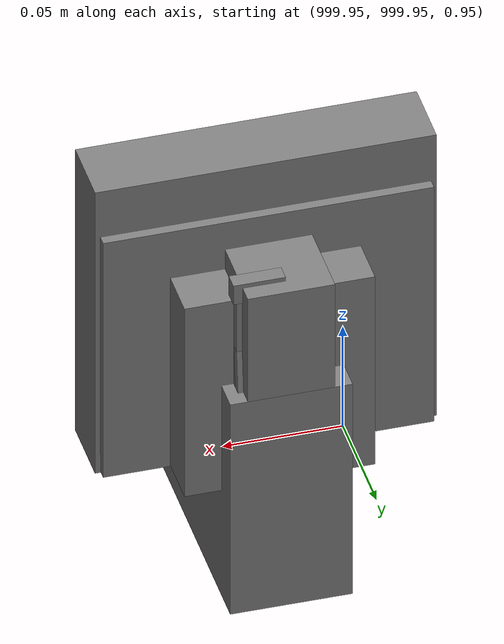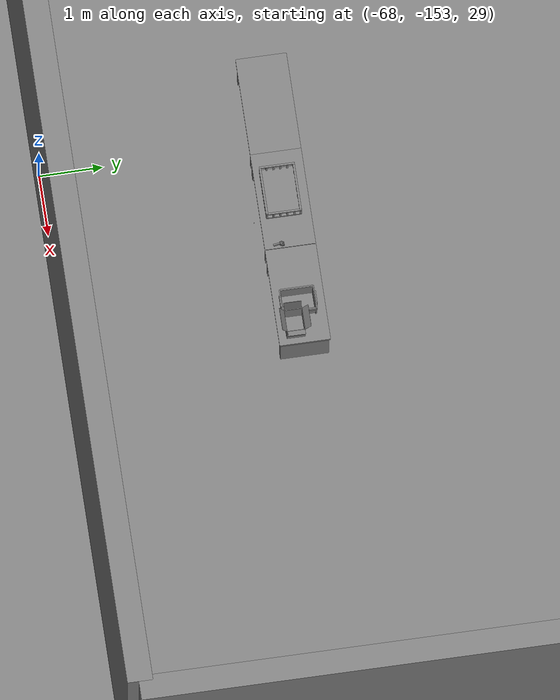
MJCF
<mujoco>
    <option gravity="0.000000000 0.000000000 -9.810000420" timestep="0.0049999999" integrator="implicitfast" density="1.225" viscosity="1.8000001e-05" noslip_iterations="10" iterations="100" sdf_iterations="50">
        <flag multiccd="disable"/>
    </option>
    <size memory="1000M"/>
    <compiler coordinate="local"/>
    <worldbody>
        <light cutoff="30" pos="0 1 1" dir="0 -1 -2"/>
        <light cutoff="30" pos="0 -1 1" dir="0 1 -2"/>
        <body pos="1000.000000000 999.999938965 1.000000000" euler="0.000000000 0.000000000 180.000000000" name="openloong_gripper_2f85_fix_base_usda_intelcore_i5">
            <geom contype="1" conaffinity="1" density="1000" type="box" material="" rgba="0.500000000 0.500000000 0.500000000 1.000000000" solimp="0.899999976 0.949999988 0.001000000" friction="1.000000000 0.005000000 0.000100000" solref="0.020000000 1.000000000" margin="0" condim="3" group="0" pos="0.000000000 0.000000000 0.051722717" quat="0.707106709 0.000000000 0.000000000 -0.707106769" size="0.052800000 0.018080002 0.052800000" name="openloong_gripper_2f85_fix_base_usda_geom_F95C3677_BF63_489C_BD38_D379D62AD82B"/>
            <freejoint name="openloong_gripper_2f85_fix_base_usda_intelcore_i5_joint"/>
            <site size="0.005000000 0.005000000 0.005000000" rgba="0.500000000 0.500000000 0.500000000 1.000000000" pos="0.000000000 0.000000000 0.000000000" quat="0.999961913 0.008726534 0.000000000 0.000000000" group="0" type="sphere" name="openloong_gripper_2f85_fix_base_usda_intelcore_i5site"/>
        </body>
        <body pos="1000.000000000 1000.000000000 1.000000000" euler="0.000011953 0.000005123 -179.999984741" name="openloong_gripper_2f85_fix_base_usda_intel_box">
            <geom contype="1" conaffinity="1" density="1000" type="box" material="" rgba="0.500000000 0.500000000 0.500000000 1.000000000" solimp="0.899999976 0.949999988 0.001000000" friction="1.000000000 0.005000000 0.000100000" solref="0.020000000 1.000000000" margin="0" condim="3" group="0" pos="0.000000000 -0.000067139 0.000082284" quat="0.707106709 0.000000225 0.000000253 0.707106650" size="0.052800003 0.025300000 0.052800003" name="openloong_gripper_2f85_fix_base_usda_geom_9AA7822A_CB97_42D6_B165_710DBC8A479A"/>
            <freejoint name="openloong_gripper_2f85_fix_base_usda_intel_box_joint"/>
            <site size="0.005000000 0.005000000 0.005000000" rgba="0.500000000 0.500000000 0.500000000 1.000000000" pos="0.000000000 0.000000000 0.000000000" quat="0.999961913 0.008726500 0.000000000 0.000000000" group="0" type="sphere" name="openloong_gripper_2f85_fix_base_usda_intel_boxsite"/>
        </body>
        <body pos="1000.000000000 1000.000000000 1.000000000" euler="0.000000000 0.000000000 180.000000000" name="openloong_gripper_2f85_fix_base_usda_cpu_fan">
            <geom contype="1" conaffinity="1" density="1000" type="box" material="" rgba="0.500000000 0.500000000 0.500000000 1.000000000" solimp="0.899999976 0.949999988 0.001000000" friction="1.000000000 0.005000000 0.000100000" solref="0.020000000 1.000000000" margin="0" condim="3" group="0" pos="0.000000000 0.000000000 0.070034981" quat="0.000000000 0.000000000 0.000000000 1.000000000" size="0.070700005 0.014699999 0.070700005" name="openloong_gripper_2f85_fix_base_usda_geom_54C3A3D0_6314_4C11_AB08_C40F4771DEF3"/>
            <freejoint name="openloong_gripper_2f85_fix_base_usda_cpu_fan_joint"/>
            <site size="0.005000000 0.005000000 0.005000000" rgba="0.500000000 0.500000000 0.500000000 1.000000000" pos="0.000000000 0.000000000 0.000000000" quat="0.999961913 0.008726535 0.000000000 0.000000000" group="0" type="sphere" name="openloong_gripper_2f85_fix_base_usda_cpu_fancsite"/>
        </body>
        <body pos="1000.000000000 1000.000000000 1.000000000" euler="0.000000000 0.000000000 180.000000000" name="openloong_gripper_2f85_fix_base_usda_battery_01">
            <geom contype="1" conaffinity="1" density="1000" type="box" material="" rgba="0.500000000 0.500000000 0.500000000 1.000000000" solimp="0.899999976 0.949999988 0.001000000" friction="1.000000000 0.005000000 0.000100000" solref="0.020000000 1.000000000" margin="0" condim="3" group="0" pos="-0.011123657 -0.041940309 0.101691343" quat="1.000000000 0.000000000 0.000000000 0.000000000" size="0.010800000 0.003375000 0.004725000" name="openloong_gripper_2f85_fix_base_usda_geom_11A26BEB_DCFB_489B_B636_30C1E2FB6C97"/>
            <geom contype="1" conaffinity="1" density="1000" type="box" material="" rgba="0.500000000 0.500000000 0.500000000 1.000000000" solimp="0.899999976 0.949999988 0.001000000" friction="1.000000000 0.005000000 0.000100000" solref="0.020000000 1.000000000" margin="0" condim="3" group="0" pos="-0.010876465 -0.044247437 0.047066893" quat="0.998702705 -0.050920475 0.000000000 0.000000000" size="0.009450001 0.002700000 0.024975000" name="openloong_gripper_2f85_fix_base_usda_geom_BF867329_FC5D_4C9A_81B5_0606945533B2"/>
            <geom contype="1" conaffinity="1" density="1000" type="box" material="" rgba="0.500000000 0.500000000 0.500000000 1.000000000" solimp="0.899999976 0.949999988 0.001000000" friction="1.000000000 0.005000000 0.000100000" solref="0.020000000 1.000000000" margin="0" condim="3" group="0" pos="-0.001235962 -0.000659180 0.047381196" quat="1.000000000 0.000000000 0.000000000 0.000000000" size="0.039420001 0.039150000 0.047250003" name="openloong_gripper_2f85_fix_base_usda_geom_F9A9EA5F_2262_4431_8B8A_8397DFDFFEEC"/>
            <geom contype="1" conaffinity="1" density="1000" type="box" material="" rgba="0.500000000 0.500000000 0.500000000 1.000000000" solimp="0.899999976 0.949999988 0.001000000" friction="1.000000000 0.005000000 0.000100000" solref="0.020000000 1.000000000" margin="0" condim="3" group="0" pos="-0.010876465 -0.039138794 0.009851727" quat="1.000000000 0.000000000 0.000000000 0.000000000" size="0.009450001 0.010800000 0.013500000" name="openloong_gripper_2f85_fix_base_usda_geom_12690C5F_583D_46DD_BD4B_D32C02C25BB1"/>
            <geom contype="1" conaffinity="1" density="1000" type="box" material="" rgba="0.500000000 0.500000000 0.500000000 1.000000000" solimp="0.899999976 0.949999988 0.001000000" friction="1.000000000 0.005000000 0.000100000" solref="0.020000000 1.000000000" margin="0" condim="3" group="0" pos="-0.010876465 -0.041528322 0.071508206" quat="1.000000000 0.000000000 0.000000000 0.000000000" size="0.009450001 0.002700000 0.027000001" name="openloong_gripper_2f85_fix_base_usda_geom_6220061C_5430_4813_9FC0_4BFBEBDC88B8"/>
            <freejoint name="openloong_gripper_2f85_fix_base_usda_battery_01_joint"/>
            <site size="0.005000000 0.005000000 0.005000000" rgba="0.500000000 0.500000000 0.500000000 1.000000000" pos="0.000000000 0.000000000 0.000000000" quat="0.999961913 0.008726500 0.000000000 0.000000000" group="0" type="sphere" name="openloong_gripper_2f85_fix_base_usda_battery_01site"/>
        </body>
        <body pos="-65.798484802 -149.372955322 31.167098999" euler="-10.686930656 -48.450805664 -10.030295372" mocap="true" name="spotlight5_SpotLight"/>
        <body pos="1000.000000000 1000.000000000 1.000000000" euler="0.000000000 0.000000000 180.000000000" name="openloong_gripper_2f85_fix_base_usda_wifi_box">
            <geom contype="1" conaffinity="1" density="1000" type="box" material="" rgba="0.500000000 0.500000000 0.500000000 1.000000000" solimp="0.899999976 0.949999988 0.001000000" friction="1.000000000 0.005000000 0.000100000" solref="0.020000000 1.000000000" margin="0" condim="3" group="0" pos="0.000000000 0.000000000 0.058978677" quat="0.000000000 0.000000047 0.000000000 1.000000000" size="0.068499997 0.018999999 0.059000000" name="openloong_gripper_2f85_fix_base_usda_geom_36DFEB1B_C350_45C8_9640_8A9732399067"/>
            <freejoint name="openloong_gripper_2f85_fix_base_usda_wifi_box_joint"/>
            <site size="0.005000000 0.005000000 0.005000000" rgba="0.500000000 0.500000000 0.500000000 1.000000000" pos="0.000000000 0.000000000 0.000000000" quat="0.999961913 0.008726500 0.000000000 0.000000000" group="0" type="sphere" name="openloong_gripper_2f85_fix_base_usda_wifi_boxsite"/>
        </body>
        <body pos="-65.961799622 -149.360580444 31.168386459" euler="160.984924316 -50.864952087 -163.491744995" mocap="true" name="spotlight3_SpotLight"/>
        <body pos="-65.888259888 -149.496841431 31.164396286" euler="-169.623962402 -87.358383179 -111.305442810" mocap="true" name="spotlight2_SpotLight"/>
        <body pos="-64.866622925 -149.383972168 30.183746338" euler="89.999984741 89.999946594 0.000000000" name="openloong_gripper_2f85_fix_base_usda_bluebox_01">
            <geom contype="1" conaffinity="1" density="1000" type="box" material="" rgba="0.500000000 0.500000000 0.500000000 1.000000000" solimp="0.899999976 0.949999988 0.001000000" friction="1.000000000 0.005000000 0.000100000" solref="0.020000000 1.000000000" margin="0" condim="3" group="0" pos="0.276580811 0.187225342 0.000068665" quat="0.707106948 0.000077471 0.707106352 0.000077486" size="0.100000001 0.057999998 0.010000000" name="openloong_gripper_2f85_fix_base_usda_geom_7ADDA3A3_1FC3_423C_BBB1_04AA2BAD1478"/>
            <geom contype="1" conaffinity="1" density="1000" type="box" material="" rgba="0.500000000 0.500000000 0.500000000 1.000000000" solimp="0.899999976 0.949999988 0.001000000" friction="1.000000000 0.005000000 0.000100000" solref="0.020000000 1.000000000" margin="0" condim="3" group="0" pos="0.000000000 0.002883911 0.000000000" quat="0.999999881 0.000000000 0.000000000 0.000000000" size="0.254000008 0.003000000 0.172000006" name="openloong_gripper_2f85_fix_base_usda_geom_E4B60CA1_B289_4190_AB42_DBD5DEE5F9ED"/>
            <geom contype="1" conaffinity="1" density="1000" type="box" material="" rgba="0.500000000 0.500000000 0.500000000 1.000000000" solimp="0.899999976 0.949999988 0.001000000" friction="1.000000000 0.005000000 0.000100000" solref="0.020000000 1.000000000" margin="0" condim="3" group="0" pos="0.000000000 0.124874115 0.173484802" quat="0.999796331 0.020176515 -0.000000015 0.000000030" size="0.259999990 0.119999997 0.007000000" name="openloong_gripper_2f85_fix_base_usda_geom_9C10BD57_07CB_4F37_BE2B_380D1FB8601D"/>
            <geom contype="1" conaffinity="1" density="1000" type="box" material="" rgba="0.500000000 0.500000000 0.500000000 1.000000000" solimp="0.899999976 0.949999988 0.001000000" friction="1.000000000 0.005000000 0.000100000" solref="0.020000000 1.000000000" margin="0" condim="3" group="0" pos="0.000000000 0.124874115 -0.173469543" quat="0.999796331 -0.020176545 -0.000000015 0.000000000" size="0.259999990 0.119999997 0.007000000" name="openloong_gripper_2f85_fix_base_usda_geom_7197A5EA_BBA1_46C5_A866_76D6280F44AE"/>
            <geom contype="1" conaffinity="1" density="1000" type="box" material="" rgba="0.500000000 0.500000000 0.500000000 1.000000000" solimp="0.899999976 0.949999988 0.001000000" friction="1.000000000 0.005000000 0.000100000" solref="0.020000000 1.000000000" margin="0" condim="3" group="0" pos="0.000000000 0.214008331 0.188980103" quat="0.999912977 0.013176724 0.000000015 0.000000000" size="0.259999990 0.029999999 0.012500000" name="openloong_gripper_2f85_fix_base_usda_geom_BC760C70_BA21_4F10_9217_93DAC406C0C9"/>
            <geom contype="1" conaffinity="1" density="1000" type="box" material="" rgba="0.500000000 0.500000000 0.500000000 1.000000000" solimp="0.899999976 0.949999988 0.001000000" friction="1.000000000 0.005000000 0.000100000" solref="0.020000000 1.000000000" margin="0" condim="3" group="0" pos="-0.258361816 0.125289917 0.001876831" quat="0.702796936 -0.020792112 0.710783124 0.020769298" size="0.189999998 0.119999997 0.009000000" name="openloong_gripper_2f85_fix_base_usda_geom_EE551577_61CF_4B96_B548_2960DCD67159"/>
            <geom contype="1" conaffinity="1" density="1000" type="box" material="" rgba="0.500000000 0.500000000 0.500000000 1.000000000" solimp="0.899999976 0.949999988 0.001000000" friction="1.000000000 0.005000000 0.000100000" solref="0.020000000 1.000000000" margin="0" condim="3" group="0" pos="0.000000000 0.214008331 -0.188980103" quat="0.999912977 -0.013176769 0.000000030 0.000000015" size="0.259999990 0.029999999 0.012500000" name="openloong_gripper_2f85_fix_base_usda_geom_D7D9645B_8A2E_4D83_BC25_FF0CDA445896"/>
            <geom contype="1" conaffinity="1" density="1000" type="box" material="" rgba="0.500000000 0.500000000 0.500000000 1.000000000" solimp="0.899999976 0.949999988 0.001000000" friction="1.000000000 0.005000000 0.000100000" solref="0.020000000 1.000000000" margin="0" condim="3" group="0" pos="-0.276611328 0.187225342 0.000068665" quat="0.707106650 0.000077441 0.707106709 0.000077456" size="0.100000001 0.057999998 0.010000000" name="openloong_gripper_2f85_fix_base_usda_geom_C78A5342_2467_4487_ADB3_1E5BA2AA5E3A"/>
            <geom contype="1" conaffinity="1" density="1000" type="box" material="" rgba="0.500000000 0.500000000 0.500000000 1.000000000" solimp="0.899999976 0.949999988 0.001000000" friction="1.000000000 0.005000000 0.000100000" solref="0.020000000 1.000000000" margin="0" condim="3" group="0" pos="0.258331299 0.125289917 0.001876831" quat="0.702851415 0.018856421 0.710823774 -0.019329369" size="0.189999998 0.119999997 0.009000000" name="openloong_gripper_2f85_fix_base_usda_geom_4CC6739A_8FA9_4CFC_837A_ADA6C57CD8CF"/>
            <freejoint name="openloong_gripper_2f85_fix_base_usda_bluebox_01_joint"/>
            <site size="0.005000000 0.005000000 0.005000000" rgba="0.500000000 0.500000000 0.500000000 1.000000000" pos="0.000000000 0.000000000 0.000000000" quat="0.999961913 0.008726534 0.000000000 0.000000000" group="0" type="sphere" name="openloong_gripper_2f85_fix_base_usda_bluebox_01site"/>
        </body>
        <body pos="-64.496299744 -149.491867065 30.235729218" euler="0.000000000 0.000000000 89.999946594" name="openloong_gripper_2f85_fix_base_usda_cardboardbox_01">
            <geom contype="1" conaffinity="1" density="1000" type="box" material="" rgba="0.500000000 0.500000000 0.500000000 1.000000000" solimp="0.899999976 0.949999988 0.001000000" friction="1.000000000 0.005000000 0.000100000" solref="0.020000000 1.000000000" margin="0" condim="3" group="0" pos="-0.003166199 -0.004086494 0.005052090" quat="1.000000000 0.000000000 0.000000000 0.000000000" size="0.142499998 0.177500010 0.005000000" name="openloong_gripper_2f85_fix_base_usda_geom_CE92EE43_C11D_4B9D_A912_33FB2EA524A0"/>
            <geom contype="1" conaffinity="1" density="1000" type="box" material="" rgba="0.500000000 0.500000000 0.500000000 1.000000000" solimp="0.899999976 0.949999988 0.001000000" friction="1.000000000 0.005000000 0.000100000" solref="0.020000000 1.000000000" margin="0" condim="3" group="0" pos="-0.003166199 0.170316696 0.150570869" quat="1.000000000 0.000000000 0.000000000 0.000000000" size="0.142499998 0.005000000 0.149999991" name="openloong_gripper_2f85_fix_base_usda_geom_E306160D_443A_4703_907D_04D264307F24"/>
            <geom contype="1" conaffinity="1" density="1000" type="box" material="" rgba="0.500000000 0.500000000 0.500000000 1.000000000" solimp="0.899999976 0.949999988 0.001000000" friction="1.000000000 0.005000000 0.000100000" solref="0.020000000 1.000000000" margin="0" condim="3" group="0" pos="-0.147399902 -0.005307198 0.150570869" quat="1.000000000 0.000000000 0.000000000 0.000000000" size="0.005000000 0.177500010 0.149999991" name="openloong_gripper_2f85_fix_base_usda_geom_E9E15134_9507_462C_AE87_6CF9842E25FF"/>
            <geom contype="1" conaffinity="1" density="1000" type="box" material="" rgba="0.500000000 0.500000000 0.500000000 1.000000000" solimp="0.899999976 0.949999988 0.001000000" friction="1.000000000 0.005000000 0.000100000" solref="0.020000000 1.000000000" margin="0" condim="3" group="0" pos="0.140275955 -0.005307198 0.150570869" quat="1.000000000 0.000000000 0.000000000 0.000000000" size="0.005000000 0.177500010 0.149999991" name="openloong_gripper_2f85_fix_base_usda_geom_B9A7F8CC_0DA1_44B4_BBFF_2B4CE10AF51E"/>
            <geom contype="1" conaffinity="1" density="1000" type="box" material="" rgba="0.500000000 0.500000000 0.500000000 1.000000000" solimp="0.899999976 0.949999988 0.001000000" friction="1.000000000 0.005000000 0.000100000" solref="0.020000000 1.000000000" margin="0" condim="3" group="0" pos="-0.003166199 -0.181550980 0.150570869" quat="1.000000000 0.000000000 0.000000000 0.000000000" size="0.142499998 0.005000000 0.149999991" name="openloong_gripper_2f85_fix_base_usda_geom_7AEB79ED_676E_42B4_B504_635B834554F6"/>
            <freejoint name="openloong_gripper_2f85_fix_base_usda_cardboardbox_01_joint"/>
            <site size="0.005000000 0.005000000 0.005000000" rgba="0.500000000 0.500000000 0.500000000 1.000000000" pos="0.000000000 0.000000000 0.000000000" quat="0.999961913 0.008726535 0.000000000 0.000000000" group="0" type="sphere" name="openloong_gripper_2f85_fix_base_usda_site_210ED27D_9C91_48EE_821F_DC29A09C258E"/>
            <body pos="0.139160156 -0.004048347 0.301930904" euler="-179.999954224 49.383502960 179.999954224" name="openloong_gripper_2f85_fix_base_usda_A1_006">
                <geom contype="1" conaffinity="1" density="1000" type="box" material="" rgba="0.500000000 0.500000000 0.500000000 1.000000000" solimp="0.899999976 0.949999988 0.001000000" friction="1.000000000 0.005000000 0.000100000" solref="0.020000000 1.000000000" margin="0" condim="3" group="0" pos="-0.071587563 0.000009537 0.001745224" quat="0.999999881 0.000000000 0.000000000 0.000000000" size="0.071249999 0.179999992 0.002500000" name="openloong_gripper_2f85_fix_base_usda_geom_67003498_02F0_4B5E_8E74_D472F4F92506"/>
                <joint armature="0" stiffness="0.07" damping="0.0099999998" axis="0.000000 1.000000 0.000000" type="hinge" name="openloong_gripper_2f85_fix_base_usda_A1_006"/>
            </body>
            <body pos="-0.145902634 -0.004086494 0.301938057" euler="-180.000000000 -60.000011444 -180.000000000" name="openloong_gripper_2f85_fix_base_usda_A2_006">
                <geom contype="1" conaffinity="1" density="1000" type="box" material="" rgba="0.500000000 0.500000000 0.500000000 1.000000000" solimp="0.899999976 0.949999988 0.001000000" friction="1.000000000 0.005000000 0.000100000" solref="0.020000000 1.000000000" margin="0" condim="3" group="0" pos="0.071268082 0.000009537 0.002717972" quat="0.000002921 0.000000000 -0.000000030 0.999999881" size="0.071249999 0.179999992 0.002500000" name="openloong_gripper_2f85_fix_base_usda_geom_85ADDB9F_DEEB_4387_8E38_B766E3401DA6"/>
                <joint armature="0" stiffness="0.07" damping="0.0099999998" axis="0.000000 1.000000 0.000000" type="hinge" name="openloong_gripper_2f85_fix_base_usda_A2_006"/>
            </body>
            <body pos="-0.003385544 0.175991058 0.301930904" euler="-125.858116150 -0.000004561 0.000002331" name="openloong_gripper_2f85_fix_base_usda_B2_006">
                <geom contype="1" conaffinity="1" density="1000" type="box" material="" rgba="0.500000000 0.500000000 0.500000000 1.000000000" solimp="0.899999976 0.949999988 0.001000000" friction="1.000000000 0.005000000 0.000100000" solref="0.020000000 1.000000000" margin="0" condim="3" group="0" pos="0.000009537 -0.070939064 -0.002470016" quat="0.999614120 0.027776197 -0.000000015 0.000000030" size="0.137500003 0.064999998 0.005000000" name="openloong_gripper_2f85_fix_base_usda_geom_3ED2D92E_36A6_42F6_8C49_529551A6AD14"/>
                <joint armature="0" stiffness="0.07" damping="0.0099999998" axis="1.000000 0.000000 0.000000" type="hinge" name="openloong_gripper_2f85_fix_base_usda_B2_006"/>
            </body>
            <body pos="-0.003385544 -0.184140205 0.301938057" euler="147.805557251 0.000000000 0.000000000" name="openloong_gripper_2f85_fix_base_usda_B1_006">
                <geom contype="1" conaffinity="1" density="1000" type="box" material="" rgba="0.500000000 0.500000000 0.500000000 1.000000000" solimp="0.899999976 0.949999988 0.001000000" friction="1.000000000 0.005000000 0.000100000" solref="0.020000000 1.000000000" margin="0" condim="3" group="0" pos="-0.000028610 0.070202351 -0.002703667" quat="0.999614179 -0.027776167 0.000000000 0.000000000" size="0.137500003 0.064999998 0.005000000" name="openloong_gripper_2f85_fix_base_usda_geom_4CB728FE_708A_4CA7_B601_B76250E8F40D"/>
                <joint armature="0" stiffness="0.07" damping="0.0099999998" axis="1.000000 0.000000 0.000000" type="hinge" name="openloong_gripper_2f85_fix_base_usda_B1_006"/>
            </body>
        </body>
        <body pos="-65.882858276 -149.481979370 30.229999542" euler="-64.487716675 0.000000000 0.000000000" name="openloong_gripper_2f85_fix_base_usda_Barcode">
            <geom contype="1" conaffinity="1" density="1000" type="box" material="" rgba="0.500000000 0.500000000 0.500000000 1.000000000" solimp="0.899999976 0.949999988 0.001000000" friction="1.000000000 0.005000000 0.000100000" solref="0.020000000 1.000000000" margin="0" condim="3" group="0" pos="0.000000000 0.013038635 0.001419067" quat="0.000000000 0.000000000 0.000000000 1.000000119" size="0.034000002 0.010000000 0.017999999" name="openloong_gripper_2f85_fix_base_usda_geom_CF78157A_210C_4880_9792_6B78322C8364"/>
            <geom contype="1" conaffinity="1" density="1000" type="box" material="" rgba="0.500000000 0.500000000 0.500000000 1.000000000" solimp="0.899999976 0.949999988 0.001000000" friction="1.000000000 0.005000000 0.000100000" solref="0.020000000 1.000000000" margin="0" condim="3" group="0" pos="0.000000000 -0.035301208 -0.007095337" quat="0.000000000 0.000000000 -0.043619365 0.999048233" size="0.028999999 0.010000000 0.020000000" name="openloong_gripper_2f85_fix_base_usda_geom_DEAF30D9_B413_466C_AB34_C3EE586A2F40"/>
            <geom contype="1" conaffinity="1" density="1000" type="box" material="" rgba="0.500000000 0.500000000 0.500000000 1.000000000" solimp="0.899999976 0.949999988 0.001000000" friction="1.000000000 0.005000000 0.000100000" solref="0.020000000 1.000000000" margin="0" condim="3" group="0" pos="0.000000000 -0.043411255 -0.011749268" quat="0.922262907 0.386563420 0.000000000 0.000000000" size="0.026000001 0.010000000 0.020000000" name="openloong_gripper_2f85_fix_base_usda_geom_32EE12E4_CA84_421E_A098_344A64A9C7E6"/>
            <geom contype="1" conaffinity="1" density="1000" type="box" material="" rgba="0.500000000 0.500000000 0.500000000 1.000000000" solimp="0.899999976 0.949999988 0.001000000" friction="1.000000000 0.005000000 0.000100000" solref="0.020000000 1.000000000" margin="0" condim="3" group="0" pos="0.000000000 -0.016967773 -0.031860352" quat="0.000000000 0.000000000 0.000000000 1.000000119" size="0.008000000 0.010000000 0.013000000" name="openloong_gripper_2f85_fix_base_usda_geom_94B96F3F_3753_43D7_BA39_DE573B1CCE46"/>
            <geom contype="1" conaffinity="1" density="1000" type="box" material="" rgba="0.500000000 0.500000000 0.500000000 1.000000000" solimp="0.899999976 0.949999988 0.001000000" friction="1.000000000 0.005000000 0.000100000" solref="0.020000000 1.000000000" margin="0" condim="3" group="0" pos="0.000000000 -0.001869202 0.000312805" quat="0.953716993 0.300705761 0.000000000 0.000000000" size="0.032000002 0.010000000 0.018999999" name="openloong_gripper_2f85_fix_base_usda_geom_88EC7D10_B3AE_403A_AEC7_E011AF82EDDD"/>
            <geom contype="1" conaffinity="1" density="1000" type="box" material="" rgba="0.500000000 0.500000000 0.500000000 1.000000000" solimp="0.899999976 0.949999988 0.001000000" friction="1.000000000 0.005000000 0.000100000" solref="0.020000000 1.000000000" margin="0" condim="3" group="0" pos="0.000000000 -0.019531250 -0.003173828" quat="0.953716993 0.300705761 0.000000000 0.000000000" size="0.030999999 0.010000000 0.020000000" name="openloong_gripper_2f85_fix_base_usda_geom_795CDDA8_44DA_4169_A415_A58A4C752B4A"/>
            <geom contype="1" conaffinity="1" density="1000" type="box" material="" rgba="0.500000000 0.500000000 0.500000000 1.000000000" solimp="0.899999976 0.949999988 0.001000000" friction="1.000000000 0.005000000 0.000100000" solref="0.020000000 1.000000000" margin="0" condim="3" group="0" pos="0.000000000 -0.035301208 -0.007095337" quat="0.953716993 0.300705761 0.000000000 0.000000000" size="0.028999999 0.010000000 0.020000000" name="openloong_gripper_2f85_fix_base_usda_geom_BDD0EE62_D223_423C_8DBB_CCAC2834B01A"/>
            <geom contype="1" conaffinity="1" density="1000" type="box" material="" rgba="0.500000000 0.500000000 0.500000000 1.000000000" solimp="0.899999976 0.949999988 0.001000000" friction="1.000000000 0.005000000 0.000100000" solref="0.020000000 1.000000000" margin="0" condim="3" group="0" pos="0.000000000 -0.042617798 -0.071121216" quat="0.000000000 0.000000000 0.000000000 1.000000119" size="0.013000000 0.021000000 0.059999999" name="openloong_gripper_2f85_fix_base_usda_geom_C3187BBC_CAEE_4D3D_A816_20AA21285F46"/>
            <freejoint name="openloong_gripper_2f85_fix_base_usda_Barcode_joint"/>
            <site size="0.005000000 0.005000000 0.005000000" rgba="0.500000000 0.500000000 0.500000000 1.000000000" pos="0.000000000 0.000000000 0.000000000" quat="1.000000000 0.000000000 0.000000000 0.000000000" group="0" type="sphere" name="openloong_gripper_2f85_fix_base_usda_Barcode_site"/>
        </body>
        <body pos="-66.745018005 -149.392349243 30.184000015" euler="0.000000000 0.000000000 89.999946594" name="[22329891374952]_Basket_01">
            <geom contype="1" conaffinity="1" density="1000" type="box" material="" rgba="0.500000000 0.500000000 0.500000000 1.000000000" solimp="0.899999976 0.949999988 0.001000000" friction="1.000000000 0.005000000 0.000100000" solref="0.020000000 1.000000000" margin="0" condim="3" group="0" pos="-0.052425385 0.389207840 0.089787483" quat="0.707107008 0.000000000 0.000000000 0.707106411" size="0.014249999 0.014249999 0.059999999" name="[22329891374952]_geom_E1CF38B1_1C71_422C_9A9F_328AB767DD5E"/>
            <geom contype="1" conaffinity="1" density="1000" type="box" material="" rgba="0.500000000 0.500000000 0.500000000 1.000000000" solimp="0.899999976 0.949999988 0.001000000" friction="1.000000000 0.005000000 0.000100000" solref="0.020000000 1.000000000" margin="0" condim="3" group="0" pos="0.264015198 -0.133043289 0.089787483" quat="0.707107008 0.000000000 0.000000000 0.707106411" size="0.014249999 0.014249999 0.059999999" name="[22329891374952]_geom_92B47779_9225_4A8D_8658_033D6F5F4517"/>
            <geom contype="1" conaffinity="1" density="1000" type="box" material="" rgba="0.500000000 0.500000000 0.500000000 1.000000000" solimp="0.899999976 0.949999988 0.001000000" friction="1.000000000 0.005000000 0.000100000" solref="0.020000000 1.000000000" margin="0" condim="3" group="0" pos="-0.264015198 -0.265548706 0.089793205" quat="0.707107008 0.000000000 0.000000000 0.707106411" size="0.014249999 0.014249999 0.059999999" name="[22329891374952]_geom_90FC5C63_B10B_4B14_8527_19DB44765AB0"/>
            <geom contype="1" conaffinity="1" density="1000" type="box" material="" rgba="0.500000000 0.500000000 0.500000000 1.000000000" solimp="0.899999976 0.949999988 0.001000000" friction="1.000000000 0.005000000 0.000100000" solref="0.020000000 1.000000000" margin="0" condim="3" group="0" pos="-0.160263062 -0.389322281 0.089793205" quat="0.707107008 0.000000000 0.000000000 0.707106411" size="0.014249999 0.014249999 0.059999999" name="[22329891374952]_geom_F294F0C1_76AB_45BC_9631_D3A96CB00095"/>
            <geom contype="1" conaffinity="1" density="1000" type="box" material="" rgba="0.500000000 0.500000000 0.500000000 1.000000000" solimp="0.899999976 0.949999988 0.001000000" friction="1.000000000 0.005000000 0.000100000" solref="0.020000000 1.000000000" margin="0" condim="3" group="0" pos="0.162265778 -0.389322281 0.089787483" quat="0.707107008 0.000000000 0.000000000 0.707106411" size="0.014249999 0.014249999 0.059999999" name="[22329891374952]_geom_B270296B_C100_446B_AF90_7D266C20F5DF"/>
            <geom contype="1" conaffinity="1" density="1000" type="box" material="" rgba="0.500000000 0.500000000 0.500000000 1.000000000" solimp="0.899999976 0.949999988 0.001000000" friction="1.000000000 0.005000000 0.000100000" solref="0.020000000 1.000000000" margin="0" condim="3" group="0" pos="0.264015198 0.389207840 0.089787483" quat="0.707107008 0.000000000 0.000000000 0.707106411" size="0.014249999 0.014249999 0.059999999" name="[22329891374952]_geom_6847B18D_3DA9_43A2_8F41_07022CD862C9"/>
            <geom contype="1" conaffinity="1" density="1000" type="box" material="" rgba="0.500000000 0.500000000 0.500000000 1.000000000" solimp="0.899999976 0.949999988 0.001000000" friction="1.000000000 0.005000000 0.000100000" solref="0.020000000 1.000000000" margin="0" condim="3" group="0" pos="-0.264015198 -0.133043289 0.089793205" quat="0.707107008 0.000000000 0.000000000 0.707106411" size="0.014249999 0.014249999 0.059999999" name="[22329891374952]_geom_5B40F06D_D28F_44A4_8791_24D695917EA5"/>
            <geom contype="1" conaffinity="1" density="1000" type="box" material="" rgba="0.500000000 0.500000000 0.500000000 1.000000000" solimp="0.899999976 0.949999988 0.001000000" friction="1.000000000 0.005000000 0.000100000" solref="0.020000000 1.000000000" margin="0" condim="3" group="0" pos="-0.264026642 0.269256592 0.089793205" quat="0.707107008 0.000000000 0.000000000 0.707106411" size="0.014249999 0.014249999 0.059999999" name="[22329891374952]_geom_8EF02723_E2F7_4903_8A97_826905F631DC"/>
            <geom contype="1" conaffinity="1" density="1000" type="box" material="" rgba="0.500000000 0.500000000 0.500000000 1.000000000" solimp="0.899999976 0.949999988 0.001000000" friction="1.000000000 0.005000000 0.000100000" solref="0.020000000 1.000000000" margin="0" condim="3" group="0" pos="0.054462433 0.389207840 0.089787483" quat="0.707107008 0.000000000 0.000000000 0.707106411" size="0.014249999 0.014249999 0.059999999" name="[22329891374952]_geom_68FAFDF2_F82C_4ACF_865D_A6AFD23B8B68"/>
            <geom contype="1" conaffinity="1" density="1000" type="box" material="" rgba="0.500000000 0.500000000 0.500000000 1.000000000" solimp="0.899999976 0.949999988 0.001000000" friction="1.000000000 0.005000000 0.000100000" solref="0.020000000 1.000000000" margin="0" condim="3" group="0" pos="0.054462433 -0.389322281 0.089787483" quat="0.707107008 0.000000000 0.000000000 0.707106411" size="0.014249999 0.014249999 0.059999999" name="[22329891374952]_geom_3527C453_5E20_469B_872A_AD1486AE82B1"/>
            <geom contype="1" conaffinity="1" density="1000" type="box" material="" rgba="0.500000000 0.500000000 0.500000000 1.000000000" solimp="0.899999976 0.949999988 0.001000000" friction="1.000000000 0.005000000 0.000100000" solref="0.020000000 1.000000000" margin="0" condim="3" group="0" pos="0.264015198 0.269256592 0.089793205" quat="0.707107008 0.000000000 0.000000000 0.707106411" size="0.014249999 0.014249999 0.059999999" name="[22329891374952]_geom_E97303D3_28E6_4054_ADCB_5A3EB64BEC5D"/>
            <geom contype="1" conaffinity="1" density="1000" type="box" material="" rgba="0.500000000 0.500000000 0.500000000 1.000000000" solimp="0.899999976 0.949999988 0.001000000" friction="1.000000000 0.005000000 0.000100000" solref="0.020000000 1.000000000" margin="0" condim="3" group="0" pos="0.264015198 -0.389322281 0.089787483" quat="0.707107008 0.000000000 0.000000000 0.707106411" size="0.014249999 0.014249999 0.059999999" name="[22329891374952]_geom_7D1CFACC_ED6E_45FF_82B4_B567CCE87644"/>
            <geom contype="1" conaffinity="1" density="1000" type="box" material="" rgba="0.500000000 0.500000000 0.500000000 1.000000000" solimp="0.899999976 0.949999988 0.001000000" friction="1.000000000 0.005000000 0.000100000" solref="0.020000000 1.000000000" margin="0" condim="3" group="0" pos="0.000000000 0.000000000 0.015998840" quat="0.707107008 0.000000000 0.000000000 0.707106411" size="0.403499991 0.279000014 0.015750000" name="[22329891374952]_geom_0B3B24A7_EBAC_49E0_8850_F5899D79AB32"/>
            <geom contype="1" conaffinity="1" density="1000" type="box" material="" rgba="0.500000000 0.500000000 0.500000000 1.000000000" solimp="0.899999976 0.949999988 0.001000000" friction="1.000000000 0.005000000 0.000100000" solref="0.020000000 1.000000000" margin="0" condim="3" group="0" pos="0.000000000 -0.389476776 0.163619041" quat="0.707107008 0.000000000 0.000000000 0.707106411" size="0.015000000 0.277500004 0.015750000" name="[22329891374952]_geom_0D824E7A_EC23_48A3_82CC_06272D9117ED"/>
            <geom contype="1" conaffinity="1" density="1000" type="box" material="" rgba="0.500000000 0.500000000 0.500000000 1.000000000" solimp="0.899999976 0.949999988 0.001000000" friction="1.000000000 0.005000000 0.000100000" solref="0.020000000 1.000000000" margin="0" condim="3" group="0" pos="0.162265778 0.389207840 0.089787483" quat="0.707107008 0.000000000 0.000000000 0.707106411" size="0.014249999 0.014249999 0.059999999" name="[22329891374952]_geom_9E2057F5_7377_42E0_8F58_7F143520BDE6"/>
            <geom contype="1" conaffinity="1" density="1000" type="box" material="" rgba="0.500000000 0.500000000 0.500000000 1.000000000" solimp="0.899999976 0.949999988 0.001000000" friction="1.000000000 0.005000000 0.000100000" solref="0.020000000 1.000000000" margin="0" condim="3" group="0" pos="0.000000000 0.389471054 0.163619041" quat="0.707107008 0.000000000 0.000000000 0.707106411" size="0.015000000 0.277500004 0.015750000" name="[22329891374952]_geom_45587ECD_6B86_49C1_B0FB_780A82242426"/>
            <geom contype="1" conaffinity="1" density="1000" type="box" material="" rgba="0.500000000 0.500000000 0.500000000 1.000000000" solimp="0.899999976 0.949999988 0.001000000" friction="1.000000000 0.005000000 0.000100000" solref="0.020000000 1.000000000" margin="0" condim="3" group="0" pos="-0.263511658 0.000000000 0.163619041" quat="0.707107008 0.000000000 0.000000000 0.707106411" size="0.403499991 0.015000000 0.015750000" name="[22329891374952]_geom_CED490E3_362D_4046_9BFC_18140E7CE630"/>
            <geom contype="1" conaffinity="1" density="1000" type="box" material="" rgba="0.500000000 0.500000000 0.500000000 1.000000000" solimp="0.899999976 0.949999988 0.001000000" friction="1.000000000 0.005000000 0.000100000" solref="0.020000000 1.000000000" margin="0" condim="3" group="0" pos="-0.264015198 0.141334534 0.089793205" quat="0.707107008 0.000000000 0.000000000 0.707106411" size="0.014249999 0.014249999 0.059999999" name="[22329891374952]_geom_3D20CA7B_F8BD_40AB_8FB4_E1B235DDFD38"/>
            <geom contype="1" conaffinity="1" density="1000" type="box" material="" rgba="0.500000000 0.500000000 0.500000000 1.000000000" solimp="0.899999976 0.949999988 0.001000000" friction="1.000000000 0.005000000 0.000100000" solref="0.020000000 1.000000000" margin="0" condim="3" group="0" pos="0.264015198 -0.265548706 0.089787483" quat="0.707107008 0.000000000 0.000000000 0.707106411" size="0.014249999 0.014249999 0.059999999" name="[22329891374952]_geom_5A0EDA81_4547_4F7C_9958_E1B6A245E843"/>
            <geom contype="1" conaffinity="1" density="1000" type="box" material="" rgba="0.500000000 0.500000000 0.500000000 1.000000000" solimp="0.899999976 0.949999988 0.001000000" friction="1.000000000 0.005000000 0.000100000" solref="0.020000000 1.000000000" margin="0" condim="3" group="0" pos="-0.160263062 0.389207840 0.089787483" quat="0.707107008 0.000000000 0.000000000 0.707106411" size="0.014249999 0.014249999 0.059999999" name="[22329891374952]_geom_F907A89A_CB03_4218_BD48_B390DD676000"/>
            <geom contype="1" conaffinity="1" density="1000" type="box" material="" rgba="0.500000000 0.500000000 0.500000000 1.000000000" solimp="0.899999976 0.949999988 0.001000000" friction="1.000000000 0.005000000 0.000100000" solref="0.020000000 1.000000000" margin="0" condim="3" group="0" pos="-0.052425385 -0.389322281 0.089787483" quat="0.707107008 0.000000000 0.000000000 0.707106411" size="0.014249999 0.014249999 0.059999999" name="[22329891374952]_geom_0C447462_7598_40C2_B4B7_B958FD6BC8B9"/>
            <geom contype="1" conaffinity="1" density="1000" type="box" material="" rgba="0.500000000 0.500000000 0.500000000 1.000000000" solimp="0.899999976 0.949999988 0.001000000" friction="1.000000000 0.005000000 0.000100000" solref="0.020000000 1.000000000" margin="0" condim="3" group="0" pos="-0.264026642 -0.389322281 0.089793205" quat="0.707107008 0.000000000 0.000000000 0.707106411" size="0.014249999 0.014249999 0.059999999" name="[22329891374952]_geom_9143EAAA_1AEC_4D4E_97A9_00471D1C55BC"/>
            <geom contype="1" conaffinity="1" density="1000" type="box" material="" rgba="0.500000000 0.500000000 0.500000000 1.000000000" solimp="0.899999976 0.949999988 0.001000000" friction="1.000000000 0.005000000 0.000100000" solref="0.020000000 1.000000000" margin="0" condim="3" group="0" pos="0.264015198 0.141334534 0.089787483" quat="0.707107008 0.000000000 0.000000000 0.707106411" size="0.014249999 0.014249999 0.059999999" name="[22329891374952]_geom_5A5770F0_3C11_45CC_86A0_D2A2E84E0DE5"/>
            <geom contype="1" conaffinity="1" density="1000" type="box" material="" rgba="0.500000000 0.500000000 0.500000000 1.000000000" solimp="0.899999976 0.949999988 0.001000000" friction="1.000000000 0.005000000 0.000100000" solref="0.020000000 1.000000000" margin="0" condim="3" group="0" pos="-0.264015198 0.389207840 0.089793205" quat="0.707107008 0.000000000 0.000000000 0.707106411" size="0.014249999 0.014249999 0.059999999" name="[22329891374952]_geom_161D2839_0188_4FF6_8AD9_59DEA27E56BA"/>
            <geom contype="1" conaffinity="1" density="1000" type="box" material="" rgba="0.500000000 0.500000000 0.500000000 1.000000000" solimp="0.899999976 0.949999988 0.001000000" friction="1.000000000 0.005000000 0.000100000" solref="0.020000000 1.000000000" margin="0" condim="3" group="0" pos="0.264015198 0.004480362 0.089787483" quat="0.707107008 0.000000000 0.000000000 0.707106411" size="0.014249999 0.014249999 0.059999999" name="[22329891374952]_geom_93DF0137_FED1_41F1_96CD_C6C4BF0B73CD"/>
            <geom contype="1" conaffinity="1" density="1000" type="box" material="" rgba="0.500000000 0.500000000 0.500000000 1.000000000" solimp="0.899999976 0.949999988 0.001000000" friction="1.000000000 0.005000000 0.000100000" solref="0.020000000 1.000000000" margin="0" condim="3" group="0" pos="0.263694763 -0.000011444 0.163619041" quat="0.707107008 0.000000000 0.000000000 0.707106411" size="0.403499991 0.015000000 0.015750000" name="[22329891374952]_geom_A15AC7DA_AC0A_4DBB_AA59_9D4FAA0533EA"/>
            <geom contype="1" conaffinity="1" density="1000" type="box" material="" rgba="0.500000000 0.500000000 0.500000000 1.000000000" solimp="0.899999976 0.949999988 0.001000000" friction="1.000000000 0.005000000 0.000100000" solref="0.020000000 1.000000000" margin="0" condim="3" group="0" pos="-0.264015198 0.004480362 0.089793205" quat="0.707107008 0.000000000 0.000000000 0.707106411" size="0.014249999 0.014249999 0.059999999" name="[22329891374952]_geom_AF2339D8_D140_4BC7_B32A_8240CA602B22"/>
            <freejoint name="[22329891374952]_joint_BF3F72F7_B78B_4D3C_B58B_644947F07660"/>
        </body>
        <body pos="0.000000000 0.000000000 0.000000000" euler="0.000000000 0.000000000 0.000000000" name="Static Objects_Static Objects">
            <geom contype="1" conaffinity="1" density="1000" type="box" material="" rgba="0.500000000 0.500000000 0.500000000 1.000000000" solimp="0.899999976 0.949999988 0.001000000" friction="1.000000000 0.005000000 0.000100000" solref="0.020000000 1.000000000" margin="0" condim="3" group="0" pos="-67.544113159 -149.365814209 29.727830887" quat="0.500000417 0.499999970 0.499999553 0.499999970" size="0.381000012 0.319999993 0.041000001" name="Static Objects_geom_672629AB_59CD_4A18_939A_866D0244E150"/>
            <geom contype="1" conaffinity="1" density="1000" type="box" material="" rgba="0.500000000 0.500000000 0.500000000 1.000000000" solimp="0.899999976 0.949999988 0.001000000" friction="1.000000000 0.005000000 0.000100000" solref="0.020000000 1.000000000" margin="0" condim="3" group="0" pos="-68.239501953 -149.365814209 30.086868286" quat="0.500000417 0.499999970 0.499999553 0.499999970" size="0.370999992 0.039500002 0.745000005" name="Static Objects_geom_07B1DED6_9B29_4E24_8ABB_A5B58B204424"/>
            <geom contype="1" conaffinity="1" density="1000" type="box" material="" rgba="0.500000000 0.500000000 0.500000000 1.000000000" solimp="0.899999976 0.949999988 0.001000000" friction="1.000000000 0.005000000 0.000100000" solref="0.020000000 1.000000000" margin="0" condim="3" group="0" pos="-68.239501953 -149.365814209 30.147235870" quat="0.500000417 0.499999970 0.499999553 0.499999970" size="0.400000006 0.022000000 0.800000012" name="Static Objects_geom_FC25E021_538B_4CDD_8B3E_42BF0DAA491E"/>
            <geom contype="1" conaffinity="1" density="1000" type="box" material="" rgba="0.500000000 0.500000000 0.500000000 1.000000000" solimp="0.899999976 0.949999988 0.001000000" friction="1.000000000 0.005000000 0.000100000" solref="0.020000000 1.000000000" margin="0" condim="3" group="0" pos="-68.934890747 -149.365814209 29.727830887" quat="0.500000417 0.499999970 0.499999553 0.499999970" size="0.381000012 0.319999993 0.041000001" name="Static Objects_geom_EA1A39A4_DB79_4782_B9A7_ED0063906EA4"/>
            <geom contype="1" conaffinity="1" density="1000" type="box" material="" rgba="0.500000000 0.500000000 0.500000000 1.000000000" solimp="0.899999976 0.949999988 0.001000000" friction="1.000000000 0.005000000 0.000100000" solref="0.020000000 1.000000000" margin="0" condim="3" group="0" pos="-68.239501953 -149.365814209 29.561563492" quat="0.500000417 0.499999970 0.499999553 0.499999970" size="0.020000000 0.022000000 0.660000026" name="Static Objects_geom_69214AAD_CE90_4A60_8CA4_363C505D98B7"/>
            <geom contype="1" conaffinity="1" density="1000" type="box" material="" rgba="0.500000000 0.500000000 0.500000000 1.000000000" solimp="0.899999976 0.949999988 0.001000000" friction="1.000000000 0.005000000 0.000100000" solref="0.020000000 1.000000000" margin="0" condim="3" group="0" pos="-65.945671082 -149.365814209 29.727830887" quat="0.500000417 0.499999970 0.499999553 0.499999970" size="0.381000012 0.319999993 0.041000001" name="Static Objects_geom_D46C8F02_C3FD_417B_82F3_C74E6F9B642F"/>
            <geom contype="1" conaffinity="1" density="1000" type="box" material="" rgba="0.500000000 0.500000000 0.500000000 1.000000000" solimp="0.899999976 0.949999988 0.001000000" friction="1.000000000 0.005000000 0.000100000" solref="0.020000000 1.000000000" margin="0" condim="3" group="0" pos="-66.641059875 -149.365814209 30.086868286" quat="0.500000417 0.499999970 0.499999553 0.499999970" size="0.370999992 0.039500002 0.745000005" name="Static Objects_geom_3F43AF0A_DABC_4A81_A71D_5B2DF8EF4BFE"/>
            <geom contype="1" conaffinity="1" density="1000" type="box" material="" rgba="0.500000000 0.500000000 0.500000000 1.000000000" solimp="0.899999976 0.949999988 0.001000000" friction="1.000000000 0.005000000 0.000100000" solref="0.020000000 1.000000000" margin="0" condim="3" group="0" pos="-66.641059875 -149.365814209 30.147235870" quat="0.500000417 0.499999970 0.499999553 0.499999970" size="0.400000006 0.022000000 0.800000012" name="Static Objects_geom_26EC50AB_0B1C_4D80_9EF4_5E8A94F4FA67"/>
            <geom contype="1" conaffinity="1" density="1000" type="box" material="" rgba="0.500000000 0.500000000 0.500000000 1.000000000" solimp="0.899999976 0.949999988 0.001000000" friction="1.000000000 0.005000000 0.000100000" solref="0.020000000 1.000000000" margin="0" condim="3" group="0" pos="-67.336448669 -149.365814209 29.727830887" quat="0.500000417 0.499999970 0.499999553 0.499999970" size="0.381000012 0.319999993 0.041000001" name="Static Objects_geom_53A6AED2_230A_4F75_AC1B_417A30CAE091"/>
            <geom contype="1" conaffinity="1" density="1000" type="box" material="" rgba="0.500000000 0.500000000 0.500000000 1.000000000" solimp="0.899999976 0.949999988 0.001000000" friction="1.000000000 0.005000000 0.000100000" solref="0.020000000 1.000000000" margin="0" condim="3" group="0" pos="-66.641059875 -149.365814209 29.561563492" quat="0.500000417 0.499999970 0.499999553 0.499999970" size="0.020000000 0.022000000 0.660000026" name="Static Objects_geom_BC153D15_FC70_415C_A533_5F58210ACC31"/>
            <geom contype="1" conaffinity="1" density="1000" type="box" material="" rgba="0.500000000 0.500000000 0.500000000 1.000000000" solimp="0.899999976 0.949999988 0.001000000" friction="1.000000000 0.005000000 0.000100000" solref="0.020000000 1.000000000" margin="0" condim="3" group="0" pos="-64.338577271 -149.365814209 29.727830887" quat="0.500000417 0.499999970 0.499999553 0.499999970" size="0.381000012 0.319999993 0.041000001" name="Static Objects_geom_57CFE1AE_1B08_44C0_847B_043D0C5691EE"/>
            <geom contype="1" conaffinity="1" density="1000" type="box" material="" rgba="0.500000000 0.500000000 0.500000000 1.000000000" solimp="0.899999976 0.949999988 0.001000000" friction="1.000000000 0.005000000 0.000100000" solref="0.020000000 1.000000000" margin="0" condim="3" group="0" pos="-65.033966064 -149.365814209 30.086868286" quat="0.500000417 0.499999970 0.499999553 0.499999970" size="0.370999992 0.039500002 0.745000005" name="Static Objects_geom_134902C6_1758_4CE9_A8A3_ECB97E05B035"/>
            <geom contype="1" conaffinity="1" density="1000" type="box" material="" rgba="0.500000000 0.500000000 0.500000000 1.000000000" solimp="0.899999976 0.949999988 0.001000000" friction="1.000000000 0.005000000 0.000100000" solref="0.020000000 1.000000000" margin="0" condim="3" group="0" pos="-65.033966064 -149.365814209 30.147235870" quat="0.500000417 0.499999970 0.499999553 0.499999970" size="0.400000006 0.022000000 0.800000012" name="Static Objects_geom_E8C18136_0C8C_443F_8303_91D015C68F6A"/>
            <geom contype="1" conaffinity="1" density="1000" type="box" material="" rgba="0.500000000 0.500000000 0.500000000 1.000000000" solimp="0.899999976 0.949999988 0.001000000" friction="1.000000000 0.005000000 0.000100000" solref="0.020000000 1.000000000" margin="0" condim="3" group="0" pos="-65.729354858 -149.365814209 29.727830887" quat="0.500000417 0.499999970 0.499999553 0.499999970" size="0.381000012 0.319999993 0.041000001" name="Static Objects_geom_57882019_86F1_414D_8195_3F8A5B0EBBB3"/>
            <geom contype="1" conaffinity="1" density="1000" type="box" material="" rgba="0.500000000 0.500000000 0.500000000 1.000000000" solimp="0.899999976 0.949999988 0.001000000" friction="1.000000000 0.005000000 0.000100000" solref="0.020000000 1.000000000" margin="0" condim="3" group="0" pos="-65.033966064 -149.365814209 29.561563492" quat="0.500000417 0.499999970 0.499999553 0.499999970" size="0.020000000 0.022000000 0.660000026" name="Static Objects_geom_C1970C6A_9C66_423F_9F67_ADEA0EF8F78F"/>
            <geom contype="1" conaffinity="1" density="1000" type="box" material="" rgba="0.500000000 0.500000000 0.500000000 1.000000000" solimp="0.899999976 0.949999988 0.001000000" friction="1.000000000 0.005000000 0.000100000" solref="0.020000000 1.000000000" margin="0" condim="3" group="0" pos="-61.754566193 -137.853729248 33.906845093" quat="0.707107067 0.000000000 0.000000000 0.707106471" size="0.759999990 0.759999990 4.500000000" name="Static Objects_geom_03E30AC2_96A6_4F0A_83FB_82A86A0D7BF5"/>
            <geom contype="1" conaffinity="1" density="1000" type="box" material="" rgba="0.500000000 0.500000000 0.500000000 1.000000000" solimp="0.899999976 0.949999988 0.001000000" friction="1.000000000 0.005000000 0.000100000" solref="0.020000000 1.000000000" margin="0" condim="3" group="0" pos="-57.511135101 -144.927108765 31.707921982" quat="1.000000000 0.000000000 0.000000000 0.000000000" size="0.200000003 8.000000000 2.299999952" name="Static Objects_geom_86F3C61B_7037_4B10_877A_983F42D951C1"/>
            <geom contype="1" conaffinity="1" density="1000" type="box" material="" rgba="0.500000000 0.500000000 0.500000000 1.000000000" solimp="0.899999976 0.949999988 0.001000000" friction="1.000000000 0.005000000 0.000100000" solref="0.020000000 1.000000000" margin="0" condim="3" group="0" pos="-80.517646790 -157.574050903 31.688196182" quat="0.707107067 0.000000000 0.000000000 0.707106471" size="0.600000024 0.600000024 2.299999952" name="Static Objects_geom_799D3BA6_3B91_4C82_86FB_541B7A163DF7"/>
            <geom contype="1" conaffinity="1" density="1000" type="box" material="" rgba="0.500000000 0.500000000 0.500000000 1.000000000" solimp="0.899999976 0.949999988 0.001000000" friction="1.000000000 0.005000000 0.000100000" solref="0.020000000 1.000000000" margin="0" condim="3" group="0" pos="-80.711044312 -147.414932251 31.666158676" quat="1.000000000 0.000000000 0.000000000 0.000000000" size="0.200000003 10.000000000 2.299999952" name="Static Objects_geom_935EC05B_5DC7_4448_A758_DB8B824A5E03"/>
            <geom contype="1" conaffinity="1" density="1000" type="box" material="" rgba="0.500000000 0.500000000 0.500000000 1.000000000" solimp="0.899999976 0.949999988 0.001000000" friction="1.000000000 0.005000000 0.000100000" solref="0.020000000 1.000000000" margin="0" condim="3" group="0" pos="-57.687217712 -137.434692383 31.688196182" quat="0.707107067 0.000000000 0.000000000 0.707106471" size="0.600000024 0.600000024 2.299999952" name="Static Objects_geom_C0609870_A756_4385_BF4E_ED9C5BFA0EBB"/>
            <geom contype="1" conaffinity="1" density="1000" type="box" material="" rgba="0.500000000 0.500000000 0.500000000 1.000000000" solimp="0.899999976 0.949999988 0.001000000" friction="1.000000000 0.005000000 0.000100000" solref="0.020000000 1.000000000" margin="0" condim="3" group="0" pos="-69.537033081 -140.263229370 31.714921951" quat="0.707107067 0.000000000 0.000000000 0.707106471" size="0.759999990 4.500000000 2.299999952" name="Static Objects_geom_F8A6DB0C_ABA5_462B_AC4A_44CCFF8507AF"/>
            <geom contype="1" conaffinity="1" density="1000" type="box" material="" rgba="0.500000000 0.500000000 0.500000000 1.000000000" solimp="0.899999976 0.949999988 0.001000000" friction="1.000000000 0.005000000 0.000100000" solref="0.020000000 1.000000000" margin="0" condim="3" group="0" pos="-80.073638916 -137.853713989 33.906845093" quat="0.707107067 0.000000000 0.000000000 0.707106471" size="0.759999990 0.759999990 4.500000000" name="Static Objects_geom_4A12B32E_31CA_4A20_9407_C46DBC4DDB40"/>
            <geom contype="1" conaffinity="1" density="1000" type="box" material="" rgba="0.500000000 0.500000000 0.500000000 1.000000000" solimp="0.899999976 0.949999988 0.001000000" friction="1.000000000 0.005000000 0.000100000" solref="0.020000000 1.000000000" margin="0" condim="3" group="0" pos="-73.406707764 -155.734664917 31.707921982" quat="1.000000000 0.000000000 0.000000000 0.000000000" size="0.200000003 3.000000000 2.299999952" name="Static Objects_geom_A701CA26_CBB0_4E23_ACE4_CBE4D99D1120"/>
            <geom contype="1" conaffinity="1" density="1000" type="box" material="" rgba="0.500000000 0.500000000 0.500000000 1.000000000" solimp="0.899999976 0.949999988 0.001000000" friction="1.000000000 0.005000000 0.000100000" solref="0.020000000 1.000000000" margin="0" condim="3" group="0" pos="-68.497543335 -137.448257446 31.707921982" quat="0.707107067 0.000000000 0.000000000 0.707106471" size="0.200000003 14.000000000 2.299999952" name="Static Objects_geom_B9D0E66E_9869_4889_8E66_4852F92BFE5F"/>
            <geom contype="1" conaffinity="1" density="1000" type="cylinder" material="" rgba="0.500000000 0.500000000 0.500000000 1.000000000" solimp="0.899999976 0.949999988 0.001000000" friction="1.000000000 0.005000000 0.000100000" solref="0.020000000 1.000000000" margin="0" condim="3" group="0" pos="-68.868522644 -142.134506226 31.711090088" quat="0.707107067 0.000000000 0.000000000 0.707106471" size="0.509999990 2.299999952 1.000000000" name="Static Objects_geom_743F16DB_DB0F_4EDB_80A4_6AE2302C1579"/>
            <geom contype="1" conaffinity="1" density="1000" type="plane" material="" rgba="0.500000000 0.500000000 0.500000000 1.000000000" solimp="0.899999976 0.949999988 0.001000000" friction="1.000000000 0.005000000 0.000100000" solref="0.020000000 1.000000000" margin="0" condim="3" group="0" pos="-72.873703003 -147.131927490 29.409669876" quat="1.000000000 0.000000000 0.000000000 0.000000000" size="18.000000000 14.000000000 1.000000000" name="Static Objects_geom_49D393F9_A912_4DB6_AE74_6BDCFD50DCE3"/>
            <geom contype="1" conaffinity="1" density="1000" type="box" material="" rgba="0.500000000 0.500000000 0.500000000 1.000000000" solimp="0.899999976 0.949999988 0.001000000" friction="1.000000000 0.005000000 0.000100000" solref="0.020000000 1.000000000" margin="0" condim="3" group="0" pos="-79.943580627 -157.782272339 31.707921982" quat="0.707107067 0.000000000 0.000000000 0.707106471" size="0.200000003 7.000000000 2.299999952" name="Static Objects_geom_A6D6E4AF_0795_4F7E_A825_8256D5032913"/>
            <geom contype="1" conaffinity="1" density="1000" type="box" material="" rgba="0.500000000 0.500000000 0.500000000 1.000000000" solimp="0.899999976 0.949999988 0.001000000" friction="1.000000000 0.005000000 0.000100000" solref="0.020000000 1.000000000" margin="0" condim="3" group="0" pos="-65.421028137 -152.903442383 31.707921982" quat="0.707107067 0.000000000 0.000000000 0.707106471" size="0.200000003 7.800000191 2.299999952" name="Static Objects_geom_979E22B7_BA1D_4CC5_8A45_9809B3B57910"/>
            <geom contype="1" conaffinity="1" density="1000" type="box" material="" rgba="0.500000000 0.500000000 0.500000000 1.000000000" solimp="0.899999976 0.949999988 0.001000000" friction="1.000000000 0.005000000 0.000100000" solref="0.020000000 1.000000000" margin="0" condim="3" group="0" pos="-74.776908875 -149.964416504 31.688196182" quat="1.000000000 0.000000000 0.000000000 0.000000000" size="0.600000024 0.409999996 2.299999952" name="Static Objects_geom_523CBD0B_9541_4CCA_9D94_5FBE0D84E85D"/>
            <geom contype="1" conaffinity="1" density="1000" type="cylinder" material="" rgba="0.500000000 0.500000000 0.500000000 1.000000000" solimp="0.899999976 0.949999988 0.001000000" friction="1.000000000 0.005000000 0.000100000" solref="0.020000000 1.000000000" margin="0" condim="3" group="0" pos="-60.161884308 -142.134506226 31.711090088" quat="0.707107067 0.000000000 0.000000000 0.707106471" size="0.509999990 2.299999952 1.000000000" name="Static Objects_geom_0D4FE24E_9AA1_4132_81F0_18E39FA42375"/>
            <geom contype="1" conaffinity="1" density="1000" type="cylinder" material="" rgba="0.500000000 0.500000000 0.500000000 1.000000000" solimp="0.899999976 0.949999988 0.001000000" friction="1.000000000 0.005000000 0.000100000" solref="0.020000000 1.000000000" margin="0" condim="3" group="0" pos="-75.382453918 -149.963455200 31.711090088" quat="0.707107067 0.000000000 0.000000000 0.707106471" size="0.409999996 2.299999952 1.000000000" name="Static Objects_geom_029B6EE6_2049_477A_B064_5C4CC71B883D"/>
            <geom contype="1" conaffinity="1" density="1000" type="cylinder" material="" rgba="0.500000000 0.500000000 0.500000000 1.000000000" solimp="0.899999976 0.949999988 0.001000000" friction="1.000000000 0.005000000 0.000100000" solref="0.020000000 1.000000000" margin="0" condim="3" group="0" pos="-74.154960632 -149.963455200 31.711090088" quat="0.707107067 0.000000000 0.000000000 0.707106471" size="0.409999996 2.299999952 1.000000000" name="Static Objects_geom_95C52150_BB88_4A8F_BA41_DD650817C1D2"/>
            <geom contype="1" conaffinity="1" density="1000" type="cylinder" material="" rgba="0.500000000 0.500000000 0.500000000 1.000000000" solimp="0.899999976 0.949999988 0.001000000" friction="1.000000000 0.005000000 0.000100000" solref="0.020000000 1.000000000" margin="0" condim="3" group="0" pos="-77.566612244 -142.134506226 31.711090088" quat="0.707107067 0.000000000 0.000000000 0.707106471" size="0.509999990 2.299999952 1.000000000" name="Static Objects_geom_E2E28119_9518_4E52_A4F8_B2A2676757CE"/>
        </body>
        <body pos="-66.291030884 -149.869689941 29.018842697" euler="0.000000000 0.000000000 89.999946594" mocap="true" name="openloong_gripper_2f85_fix_base_usda_leftHandMocap"/>
        <body pos="-66.291030884 -149.869689941 29.018842697" euler="0.000000000 0.000000000 89.999946594" mocap="true" name="openloong_gripper_2f85_fix_base_usda_rightHandMocap"/>
        <body pos="-66.291030884 -149.869689941 30.218843460" euler="0.000000000 0.000000000 89.999946594" name="openloong_gripper_2f85_fix_base_usda_base_link">
            <geom contype="1" conaffinity="1" density="1000" type="mesh" material="" rgba="0.783999979 0.783999979 0.783999979 1.000000000" solimp="0.899999976 0.949999988 0.001000000" friction="1.000000000 0.005000000 0.000100000" solref="0.020000000 1.000000000" margin="0" condim="3" group="3" mesh="base_link" pos="0.000000000 0.000000000 0.000000000" quat="1.000000000 0.000000000 0.000000000 0.000000000" size="1.000000000 1.000000000 1.000000000" name="openloong_gripper_2f85_fix_base_usda__geom_7_76687FCB_111A_42BD_A831_CB92F26E3772"/>
            <site size="0.005000000 0.005000000 0.005000000" rgba="0.500000000 0.500000000 0.500000000 1.000000000" pos="0.000000000 0.000000000 0.000000000" quat="1.000000000 0.000000000 0.000000000 0.000000000" group="0" type="sphere" name="openloong_gripper_2f85_fix_base_usda_imu"/>
            <inertial mass="22.447001" pos="-0.005664100 -0.001336700 0.238289997" diaginertia="0.374352545 0.277180195 0.220617250" quat="0.999247074 0.035235517 -0.015086859 0.006023135"/>
            <body pos="0.000000000 0.000000000 0.299997330" euler="0.000000000 0.000000000 0.000000000" name="openloong_gripper_2f85_fix_base_usda_dummy_body">
                <geom contype="1" conaffinity="1" density="1000" type="sphere" material="" rgba="0.783999979 0.783999979 0.783999979 1.000000000" solimp="0.899999976 0.949999988 0.001000000" friction="1.000000000 0.005000000 0.000100000" solref="0.020000000 1.000000000" margin="0" condim="3" group="3" pos="0.000000000 0.000000000 0.000000000" quat="1.000000000 0.000000000 0.000000000 0.000000000" size="0.010000000 0.000000000 0.000000000" name="openloong_gripper_2f85_fix_base_usda__geom_8_B4A25C7A_590A_45A0_B649_5A3D8E06758F"/>
                <joint armature="0.0099999998" stiffness="0" damping="0.1" axis="0.000000 0.000000 1.000000" type="hinge" name="openloong_gripper_2f85_fix_base_usda_dummy_joint"/>
                <site size="0.010000000 0.005000000 0.005000000" rgba="0.500000000 0.500000000 0.500000000 1.000000000" pos="0.000000000 0.000000000 0.000000000" quat="1.000000000 0.000000000 0.000000000 0.000000000" group="3" type="sphere" name="openloong_gripper_2f85_fix_base_usda_dummy_site"/>
            </body>
            <body pos="0.009002686 0.000000000 0.406400681" euler="0.000000000 0.000000000 0.000000000" name="openloong_gripper_2f85_fix_base_usda_Link_head_yaw">
                <geom contype="1" conaffinity="1" density="1000" type="mesh" material="" rgba="0.783999979 0.783999979 0.783999979 1.000000000" solimp="0.899999976 0.949999988 0.001000000" friction="1.000000000 0.005000000 0.000100000" solref="0.020000000 1.000000000" margin="0" condim="3" group="3" mesh="Link_head_yaw" pos="0.000000000 0.000000000 0.000000000" quat="1.000000000 0.000000000 0.000000000 0.000000000" size="1.000000000 1.000000000 1.000000000" name="openloong_gripper_2f85_fix_base_usda__geom_10_AFD023A5_CAA1_412A_A06D_C7597EA2BD05"/>
                <inertial mass="0.84249002" pos="0.000000000 -0.002081400 0.044801001" diaginertia="0.000700588 0.000629000 0.000553812" quat="0.706933022 -0.015675601 0.015677100 0.706933022"/>
                <body pos="0.000000000 -0.034599304 0.048500061" euler="0.000000000 0.000000000 0.000000000" name="openloong_gripper_2f85_fix_base_usda_Link_head_pitch">
                    <geom contype="1" conaffinity="1" density="1000" type="mesh" material="" rgba="0.783999979 0.783999979 0.783999979 1.000000000" solimp="0.899999976 0.949999988 0.001000000" friction="1.000000000 0.005000000 0.000100000" solref="0.020000000 1.000000000" margin="0" condim="3" group="3" mesh="Link_head_pitch" pos="0.000000000 0.000000000 0.000000000" quat="1.000000000 0.000000000 0.000000000 0.000000000" size="1.000000000 1.000000000 1.000000000" name="openloong_gripper_2f85_fix_base_usda__geom_12_C54FAB25_3908_4602_A21B_032B7F5DE23C"/>
                    <inertial mass="1.3943" pos="0.020569000 0.033004001 0.125000000" diaginertia="0.006381400 0.006289940 0.004481460" quat="0.973390222 0.008406822 0.228157058 0.019624906"/>
                    <body pos="0.000000000 0.029998779 0.000000000" euler="0.000000000 0.000000000 0.000000000" name="openloong_gripper_2f85_fix_base_usda_neck_center_body">
                        <site size="0.010000000 0.005000000 0.005000000" rgba="0.500000000 0.500000000 0.500000000 1.000000000" pos="0.000000000 0.000000000 0.000000000" quat="1.000000000 0.000000000 0.000000000 0.000000000" group="3" type="sphere" name="openloong_gripper_2f85_fix_base_usda_neck_center_site"/>
                        <body pos="0.020004272 0.000000000 0.149999619" euler="-0.000002229 39.998176575 -90.000205994" name="openloong_gripper_2f85_fix_base_usda_camera_head">
                            <site size="0.010000000 0.005000000 0.005000000" rgba="0.500000000 0.500000000 0.500000000 1.000000000" pos="0.000000000 0.000000000 0.000000000" quat="1.000000000 0.000000000 0.000000000 0.000000000" group="3" type="sphere" name="openloong_gripper_2f85_fix_base_usda_camera_head_site"/>
                        </body>
                    </body>
                </body>
            </body>
            <body pos="0.003997803 -0.161598206 0.392200470" euler="0.000000000 0.000000000 0.000000000" name="openloong_gripper_2f85_fix_base_usda_Link_arm_r_01">
                <geom contype="1" conaffinity="1" density="1000" type="mesh" material="" rgba="0.783999979 0.783999979 0.783999979 1.000000000" solimp="0.899999976 0.949999988 0.001000000" friction="1.000000000 0.005000000 0.000100000" solref="0.020000000 1.000000000" margin="0" condim="3" group="3" mesh="Link_arm_r_01" pos="0.000000000 0.000000000 0.000000000" quat="1.000000000 0.000000000 0.000000000 0.000000000" size="1.000000000 1.000000000 1.000000000" name="openloong_gripper_2f85_fix_base_usda__geom_14_7CEA6BC8_C492_4DF9_846A_517D0E3B4275"/>
                <joint armature="0.0099999998" stiffness="0" damping="1" axis="0.000000 -1.000000 0.000000" limited="true" range="-170.000015259 170.000015259" type="hinge" name="openloong_gripper_2f85_fix_base_usda_J_arm_r_01"/>
                <inertial mass="0.75641" pos="0.004494600 -0.038293999 -0.000001874" diaginertia="0.000842990 0.000803050 0.000587120" quat="-0.000163502 0.707098067 0.000812463 0.707115054"/>
                <body pos="-0.041992188 -0.041000366 0.000000000" euler="0.000000000 0.000000000 0.000000000" name="openloong_gripper_2f85_fix_base_usda_Link_arm_r_02">
                    <geom contype="1" conaffinity="1" density="1000" type="mesh" material="" rgba="0.783999979 0.783999979 0.783999979 1.000000000" solimp="0.899999976 0.949999988 0.001000000" friction="1.000000000 0.005000000 0.000100000" solref="0.020000000 1.000000000" margin="0" condim="3" group="3" mesh="Link_arm_r_02" pos="0.000000000 0.000000000 0.000000000" quat="1.000000000 0.000000000 0.000000000 0.000000000" size="1.000000000 1.000000000 1.000000000" name="openloong_gripper_2f85_fix_base_usda__geom_16_4582035C_5B15_4F55_8EFC_BA09726E3F4C"/>
                    <joint armature="0.0099999998" stiffness="0" damping="1" axis="-1.000000 0.000000 0.000000" limited="true" range="-105.000244141 105.000244141" type="hinge" name="openloong_gripper_2f85_fix_base_usda_J_arm_r_02"/>
                    <inertial mass="0.98500001" pos="0.041999999 -0.067430697 0.000000000" diaginertia="0.002262690 0.001730990 0.001154020" quat="0.500000000 0.500000000 -0.500000000 0.500000000"/>
                    <body pos="0.041992188 -0.122596741 0.000000000" euler="0.000000000 0.000000000 0.000000000" name="openloong_gripper_2f85_fix_base_usda_Link_arm_r_03">
                        <geom contype="1" conaffinity="1" density="1000" type="mesh" material="" rgba="0.783999979 0.783999979 0.783999979 1.000000000" solimp="0.899999976 0.949999988 0.001000000" friction="1.000000000 0.005000000 0.000100000" solref="0.020000000 1.000000000" margin="0" condim="3" group="3" mesh="Link_arm_r_03" pos="0.000000000 0.000000000 0.000000000" quat="1.000000000 0.000000000 0.000000000 0.000000000" size="1.000000000 1.000000000 1.000000000" name="openloong_gripper_2f85_fix_base_usda__geom_18_D7E839B1_E12E_47F6_ADBA_21835795813A"/>
                        <joint armature="0.0099999998" stiffness="0" damping="1" axis="0.000000 -1.000000 0.000000" limited="true" range="-170.000015259 170.000015259" type="hinge" name="openloong_gripper_2f85_fix_base_usda_J_arm_r_03"/>
                        <inertial mass="0.95899999" pos="-0.001413580 -0.164663002 0.020757901" diaginertia="0.002101340 0.002064590 0.000754802" quat="0.560480952 0.454391927 -0.443732947 0.531497955"/>
                        <body pos="0.035293579 -0.177406311 0.023998260" euler="0.000000000 0.000000000 0.000000000" name="openloong_gripper_2f85_fix_base_usda_Link_arm_r_04">
                            <geom contype="1" conaffinity="1" density="1000" type="mesh" material="" rgba="0.783999979 0.783999979 0.783999979 1.000000000" solimp="0.899999976 0.949999988 0.001000000" friction="1.000000000 0.005000000 0.000100000" solref="0.020000000 1.000000000" margin="0" condim="3" group="3" mesh="Link_arm_r_04" pos="0.000000000 0.000000000 0.000000000" quat="1.000000000 0.000000000 0.000000000 0.000000000" size="1.000000000 1.000000000 1.000000000" name="openloong_gripper_2f85_fix_base_usda__geom_20_6BEB02F7_E595_4738_934B_CA9AE0F64D7B"/>
                            <joint armature="0.0099999998" stiffness="0" damping="1" axis="-1.000000 0.000000 0.000000" limited="true" range="0.000000000 170.000015259" type="hinge" name="openloong_gripper_2f85_fix_base_usda_J_arm_r_04"/>
                            <inertial mass="0.60000002" pos="-0.038727000 -0.060766999 -0.021003000" diaginertia="0.001092610 0.000712422 0.000645102" quat="0.327701002 0.632602990 -0.467366993 0.523443997"/>
                            <body pos="-0.035293579 -0.103492737 -0.023998260" euler="0.000000000 0.000000000 0.000000000" name="openloong_gripper_2f85_fix_base_usda_Link_arm_r_05">
                                <geom contype="1" conaffinity="1" density="1000" type="mesh" material="" rgba="0.783999979 0.783999979 0.783999979 1.000000000" solimp="0.899999976 0.949999988 0.001000000" friction="1.000000000 0.005000000 0.000100000" solref="0.020000000 1.000000000" margin="0" condim="3" group="3" mesh="Link_arm_r_05" pos="0.000000000 0.000000000 0.000000000" quat="1.000000000 0.000000000 0.000000000 0.000000000" size="1.000000000 1.000000000 1.000000000" name="openloong_gripper_2f85_fix_base_usda__geom_22_0F692EA7_46C1_40D0_B89E_6E2D3C61F7A9"/>
                                <joint armature="0.0099999998" stiffness="0" damping="1" axis="0.000000 -1.000000 0.000000" limited="true" range="-170.000015259 170.000015259" type="hinge" name="openloong_gripper_2f85_fix_base_usda_J_arm_r_05"/>
                                <inertial mass="0.68976003" pos="0.000032712 -0.068658002 -0.000111780" diaginertia="0.002522510 0.002411100 0.000448695" quat="0.707660973 0.706543028 -0.002603360 0.002470550"/>
                                <body pos="-0.026489258 -0.196502686 0.000000000" euler="0.000000000 0.000000000 0.000000000" name="openloong_gripper_2f85_fix_base_usda_Link_arm_r_06">
                                    <geom contype="1" conaffinity="1" density="1000" type="mesh" material="" rgba="0.783999979 0.783999979 0.783999979 1.000000000" solimp="0.899999976 0.949999988 0.001000000" friction="1.000000000 0.005000000 0.000100000" solref="0.020000000 1.000000000" margin="0" condim="3" group="3" mesh="Link_arm_r_06" pos="0.000000000 0.000000000 0.000000000" quat="1.000000000 0.000000000 0.000000000 0.000000000" size="1.000000000 1.000000000 1.000000000" name="openloong_gripper_2f85_fix_base_usda__geom_24_83F5F8ED_3CD7_4BE5_B8BF_35385224CF01"/>
                                    <joint armature="0.0099999998" stiffness="0" damping="1" axis="1.000000 0.000000 0.000000" limited="true" range="-105.000244141 105.000244141" type="hinge" name="openloong_gripper_2f85_fix_base_usda_J_arm_r_06"/>
                                    <inertial mass="0.28" pos="0.026078001 -0.000000896 0.001663700" diaginertia="0.000156930 0.000145601 0.000104979" quat="0.707080841 0.001851080 0.001883810 0.707127810"/>
                                    <body pos="0.026489258 0.000000000 0.031799316" euler="0.000000000 0.000000000 0.000000000" name="openloong_gripper_2f85_fix_base_usda_Link_arm_r_07">
                                        <geom contype="1" conaffinity="1" density="1000" type="mesh" material="" rgba="0.783999979 0.783999979 0.783999979 1.000000000" solimp="0.899999976 0.949999988 0.001000000" friction="1.000000000 0.005000000 0.000100000" solref="0.020000000 1.000000000" margin="0" condim="3" group="3" mesh="Link_arm_r_07" pos="0.000000000 0.000000000 0.000000000" quat="1.000000000 0.000000000 0.000000000 0.000000000" size="1.000000000 1.000000000 1.000000000" name="openloong_gripper_2f85_fix_base_usda__geom_26_44C4CC56_34CB_4420_A88E_217F721CBA73"/>
                                        <joint armature="0.0099999998" stiffness="0" damping="1" axis="0.000000 0.000000 1.000000" limited="true" range="-60.000133514 60.000133514" type="hinge" name="openloong_gripper_2f85_fix_base_usda_J_arm_r_07"/>
                                        <inertial mass="0.61353999" pos="-0.007859000 -0.158170000 -0.027736001" diaginertia="0.003037610 0.002570910 0.000729379" quat="0.427542925 0.443532884 -0.553093910 0.560867906"/>
                                        <body pos="0.000000000 0.286994934 -0.270000458" euler="150.000350952 -0.000001649 -0.000000442" name="openloong_gripper_2f85_fix_base_usda_camera_wrist_r">
                                            <site size="0.010000000 0.005000000 0.005000000" rgba="0.500000000 0.500000000 0.500000000 1.000000000" pos="0.000000000 0.000000000 0.000000000" quat="1.000000000 0.000000000 0.000000000 0.000000000" group="3" type="sphere" name="openloong_gripper_2f85_fix_base_usda_camera_wrist_r_site"/>
                                        </body>
                                        <body pos="0.000000000 -0.220008850 -0.033002853" euler="0.000000000 0.000000000 179.999969482" name="openloong_gripper_2f85_fix_base_usda_ee_center_body_r">
                                            <site size="0.010000000 0.005000000 0.005000000" rgba="0.500000000 0.500000000 0.500000000 1.000000000" pos="0.000000000 0.000000000 0.000000000" quat="1.000000000 0.000000000 0.000000000 0.000000000" group="3" type="sphere" name="openloong_gripper_2f85_fix_base_usda_ee_center_site_r"/>
                                        </body>
                                        <body pos="0.000000000 -0.066001892 -0.031000137" euler="89.999984741 0.000000000 180.000000000" name="openloong_gripper_2f85_fix_base_usda_zbr_base_link">
                                            <geom contype="1" conaffinity="1" density="1000" type="mesh" material="" rgba="0.783999979 0.783999979 0.783999979 1.000000000" solimp="0.899999976 0.949999988 0.001000000" friction="1.000000000 0.005000000 0.000100000" solref="0.020000000 1.000000000" margin="0" condim="3" group="3" mesh="base" pos="0.000000000 0.000003815 -0.000007629" quat="1.000000000 0.000000000 0.000000000 0.000000000" size="1.000000238 1.000000238 1.000000238" name="openloong_gripper_2f85_fix_base_usda__geom_30_43AD582F_3A4C_4159_BD9B_2BB8FE1E88A5"/>
                                            <inertial mass="0.77744102" pos="0.000000000 -0.000027039 0.035467502" diaginertia="0.000260285 0.000225381 0.000152708" quat="0.999998808 -0.001528488 0.000000000 0.000000000"/>
                                            <body pos="-0.030609138 0.004745484 0.065696731" euler="-89.999984741 -0.000000000 0.000000000" name="openloong_gripper_2f85_fix_base_usda_r_left_driver">
                                                <geom contype="1" conaffinity="1" density="1000" type="mesh" material="" rgba="0.783999979 0.783999979 0.783999979 1.000000000" solimp="0.899999976 0.949999988 0.001000000" friction="1.000000000 0.005000000 0.000100000" solref="0.020000000 1.000000000" margin="0" condim="3" group="3" mesh="driver" pos="0.030609138 0.054901138 -0.004699708" quat="0.707106829 0.707106709 0.000000000 -0.000000000" size="1.000000238 1.000000238 1.000000238" name="openloong_gripper_2f85_fix_base_usda__geom_32_7DF3331A_CBFA_42CF_BD99_6259BF300DB1"/>
                                                <joint armature="0.0049999999" stiffness="0" damping="0.1" axis="0.000000 0.000000 1.000000" limited="true" range="0.000000000 51.566200256" type="hinge" name="openloong_gripper_2f85_fix_base_usda_r_left_driver_joint"/>
                                                <inertial mass="0.0089956298" pos="0.000000000 0.017754700 0.001073140" diaginertia="0.000001724 0.000001609 0.000000322" quat="0.681301236 0.732003212 0.000000000 0.000000000"/>
                                                <body pos="-0.031402595 0.004524232 -0.010200503" euler="0.000000000 0.000000000 180.000000000" name="openloong_gripper_2f85_fix_base_usda_r_left_coupler">
                                                    <geom contype="1" conaffinity="1" density="1000" type="mesh" material="" rgba="0.783999979 0.783999979 0.783999979 1.000000000" solimp="0.899999976 0.949999988 0.001000000" friction="1.000000000 0.005000000 0.000100000" solref="0.020000000 1.000000000" margin="0" condim="3" group="3" mesh="coupler" pos="-0.062011734 -0.050354015 0.005500795" quat="0.707106829 -0.707106709 0.000000000 -0.000000000" size="1.000000238 1.000000238 1.000000238" name="openloong_gripper_2f85_fix_base_usda__geom_34_2D157000_9BC7_49A0_A24B_7E1E429A0894"/>
                                                    <inertial mass="0.0140974" pos="0.000000000 0.003012090 0.023217499" diaginertia="0.000004162 0.000003522 0.000000888" quat="0.705635548 -0.045590367 0.045590367 0.705635548"/>
                                                </body>
                                            </body>
                                            <body pos="-0.012695315 -0.012001040 0.072212234" euler="-89.999984741 -0.000000000 0.000000000" name="openloong_gripper_2f85_fix_base_usda_r_left_spring_link">
                                                <geom contype="1" conaffinity="1" density="1000" type="mesh" material="" rgba="0.783999979 0.783999979 0.783999979 1.000000000" solimp="0.899999976 0.949999988 0.001000000" friction="1.000000000 0.005000000 0.000100000" solref="0.020000000 1.000000000" margin="0" condim="3" group="3" mesh="spring_link" pos="0.012695315 0.061416641 0.012050631" quat="0.707106829 0.707106709 0.000000000 -0.000000000" size="1.000000238 1.000000238 1.000000238" name="openloong_gripper_2f85_fix_base_usda__geom_36_B7CF7645_C39B_46C7_9908_A281F3152DD2"/>
                                                <joint armature="0.001" stiffness="0.050000001" damping="0.00125" axis="0.000000 0.000000 1.000000" limited="true" range="-17.000000000 51.566200256" type="hinge" name="openloong_gripper_2f85_fix_base_usda_r_left_spring_link_joint"/>
                                                <inertial mass="0.0221642" pos="-0.000000009 0.018162400 0.021265799" diaginertia="0.000008969 0.000006717 0.000002639" quat="0.663403213 -0.244737089 0.244737089 0.663403213"/>
                                                <body pos="-0.038208015 -0.042503368 0.002950669" euler="180.000000000 0.000000000 -0.002185660" name="openloong_gripper_2f85_fix_base_usda_r_left_follower">
                                                    <geom contype="1" conaffinity="1" density="1000" type="mesh" material="" rgba="0.783999979 0.783999979 0.783999979 1.000000000" solimp="0.899999976 0.949999988 0.001000000" friction="1.000000000 0.005000000 0.000100000" solref="0.020000000 1.000000000" margin="0" condim="3" group="3" mesh="tongue" pos="0.050918590 -0.103920005 -0.009099962" quat="0.707106829 -0.707106709 0.000000030 0.000000030" size="1.000000238 1.000000238 1.000000238" name="openloong_gripper_2f85_fix_base_usda__geom_40_A4849729_81FE_490B_B384_3B7FC84F31E6"/>
                                                    <geom contype="1" conaffinity="1" density="1000" type="mesh" material="" rgba="0.783999979 0.783999979 0.783999979 1.000000000" solimp="0.899999976 0.949999988 0.001000000" friction="1.000000000 0.005000000 0.000100000" solref="0.020000000 1.000000000" margin="0" condim="3" group="3" mesh="follower" pos="0.050918590 -0.103920005 -0.009099962" quat="0.707106829 -0.707106709 0.000000030 0.000000030" size="1.000000238 1.000000238 1.000000238" name="openloong_gripper_2f85_fix_base_usda__geom_39_78E91F88_A852_40F1_8D1D_316D438FC0CA"/>
                                                    <joint armature="0.001" stiffness="0" damping="0.1" axis="0.000000 0.000000 1.000000" limited="true" range="-49.999961853 51.566200256" type="hinge" name="openloong_gripper_2f85_fix_base_usda_r_left_follower"/>
                                                    <inertial mass="0.0125222" pos="0.000000000 -0.011046000 0.012478600" diaginertia="0.000002674 0.000002456 0.000000602" quat="0.986436546 0.164143041 0.000000000 0.000000000"/>
                                                    <body pos="-0.037765510 -0.103912376 -0.009099962" euler="-89.999984741 0.000000000 0.000004829" name="openloong_gripper_2f85_fix_base_usda_r_left_pad">
                                                        <geom contype="1" conaffinity="1" density="1000" type="box" material="" rgba="0.550000012 0.550000012 0.550000012 1.000000000" solimp="0.949999988 0.990000010 0.001000000" friction="0.699999988 0.005000000 0.000100000" solref="0.020000000 1.000000000" margin="0" condim="3" group="3" mass="1e-06" pos="0.043243419 0.000003815 0.119995147" quat="0.999999881 0.000000000 0.000000000 0.000000000" size="0.002000001 0.011000003 0.009375002" name="openloong_gripper_2f85_fix_base_usda_r_left_pad1_8101D3D2_2B00_40FE_ADEE_E66A9729A487"/>
                                                        <geom contype="1" conaffinity="1" density="1000" type="box" material="" rgba="0.449999988 0.449999988 0.449999988 1.000000000" solimp="0.949999988 0.990000010 0.001000000" friction="0.600000024 0.005000000 0.000100000" solref="0.020000000 1.000000000" margin="0" condim="3" group="3" mass="1e-06" pos="0.043243419 0.000003815 0.138748199" quat="0.999999881 0.000000000 0.000000000 0.000000000" size="0.002000001 0.011000003 0.009375002" name="openloong_gripper_2f85_fix_base_usda_r_left_pad2_CF4FF217_9A46_4CFC_B1C4_C00DBF704DB4"/>
                                                    </body>
                                                </body>
                                            </body>
                                            <body pos="0.030593880 -0.004753114 0.065696731" euler="89.999984741 0.000000000 180.000000000" name="openloong_gripper_2f85_fix_base_usda_r_right_driver">
                                                <geom contype="1" conaffinity="1" density="1000" type="mesh" material="" rgba="0.783999979 0.783999979 0.783999979 1.000000000" solimp="0.899999976 0.949999988 0.001000000" friction="1.000000000 0.005000000 0.000100000" solref="0.020000000 1.000000000" margin="0" condim="3" group="3" mesh="driver" pos="0.030593880 0.054901138 -0.004699708" quat="0.707106829 0.707106709 0.000000000 0.000000000" size="1.000000238 1.000000238 1.000000238" name="openloong_gripper_2f85_fix_base_usda__geom_42_EEC636E4_EC5F_45CE_AD88_ED1509C544E6"/>
                                                <joint armature="0.0049999999" stiffness="0" damping="0.1" axis="0.000000 0.000000 1.000000" limited="true" range="0.000000000 51.566200256" type="hinge" name="openloong_gripper_2f85_fix_base_usda_r_right_driver_joint"/>
                                                <inertial mass="0.0089956298" pos="0.000000000 0.017754700 0.001073140" diaginertia="0.000001724 0.000001609 0.000000322" quat="0.681301236 0.732003212 0.000000000 0.000000000"/>
                                                <body pos="-0.031417854 0.004531861 -0.010202411" euler="0.000000000 0.000000000 180.000000000" name="openloong_gripper_2f85_fix_base_usda_r_right_coupler">
                                                    <geom contype="1" conaffinity="1" density="1000" type="mesh" material="" rgba="0.783999979 0.783999979 0.783999979 1.000000000" solimp="0.899999976 0.949999988 0.001000000" friction="1.000000000 0.005000000 0.000100000" solref="0.020000000 1.000000000" margin="0" condim="3" group="3" mesh="coupler" pos="-0.062042251 -0.050376903 0.005500795" quat="0.707106829 -0.707106709 0.000000000 0.000000000" size="1.000000238 1.000000238 1.000000238" name="openloong_gripper_2f85_fix_base_usda__geom_44_15FAA692_655B_40CA_BAF3_ADC460A75BEF"/>
                                                    <inertial mass="0.0140974" pos="0.000000000 0.003012090 0.023217499" diaginertia="0.000004162 0.000003522 0.000000888" quat="0.705635548 -0.045590367 0.045590367 0.705635548"/>
                                                </body>
                                            </body>
                                            <body pos="0.012695315 0.011997226 0.072219864" euler="89.999984741 0.000000000 180.000000000" name="openloong_gripper_2f85_fix_base_usda_r_right_spring_link">
                                                <geom contype="1" conaffinity="1" density="1000" type="mesh" material="" rgba="0.783999979 0.783999979 0.783999979 1.000000000" solimp="0.899999976 0.949999988 0.001000000" friction="1.000000000 0.005000000 0.000100000" solref="0.020000000 1.000000000" margin="0" condim="3" group="3" mesh="spring_link" pos="0.012695315 0.061424270 0.012048724" quat="0.707106829 0.707106709 0.000000000 0.000000000" size="1.000000238 1.000000238 1.000000238" name="openloong_gripper_2f85_fix_base_usda__geom_46_49C19208_164D_4FEE_B413_5BCF215D5652"/>
                                                <joint armature="0.001" stiffness="0.050000001" damping="0.00125" axis="0.000000 0.000000 1.000000" limited="true" range="-17.000000000 51.566200256" type="hinge" name="openloong_gripper_2f85_fix_base_usda_r_right_spring_link_joint"/>
                                                <inertial mass="0.0221642" pos="-0.000000009 0.018162400 0.021265799" diaginertia="0.000008969 0.000006717 0.000002639" quat="0.663403213 -0.244737089 0.244737089 0.663403213"/>
                                                <body pos="-0.038208015 -0.042495739 0.002950669" euler="180.000000000 0.000000000 0.000000000" name="openloong_gripper_2f85_fix_base_usda_r_right_follower">
                                                    <geom contype="1" conaffinity="1" density="1000" type="mesh" material="" rgba="0.783999979 0.783999979 0.783999979 1.000000000" solimp="0.899999976 0.949999988 0.001000000" friction="1.000000000 0.005000000 0.000100000" solref="0.020000000 1.000000000" margin="0" condim="3" group="3" mesh="follower" pos="0.050888073 -0.103927635 -0.009099962" quat="0.707106829 -0.707106709 0.000000000 0.000000000" size="1.000000238 1.000000238 1.000000238" name="openloong_gripper_2f85_fix_base_usda__geom_50_AF232D77_7A75_457C_8CE9_C7CF3BDEF655"/>
                                                    <geom contype="1" conaffinity="1" density="1000" type="mesh" material="" rgba="0.783999979 0.783999979 0.783999979 1.000000000" solimp="0.899999976 0.949999988 0.001000000" friction="1.000000000 0.005000000 0.000100000" solref="0.020000000 1.000000000" margin="0" condim="3" group="3" mesh="tongue" pos="0.050888073 -0.103927635 -0.009099962" quat="0.707106829 -0.707106709 0.000000000 0.000000000" size="1.000000238 1.000000238 1.000000238" name="openloong_gripper_2f85_fix_base_usda__geom_49_60E6BD9F_1A10_4ADA_AB61_9FCCBF212077"/>
                                                    <joint armature="0.001" stiffness="0" damping="0.1" axis="0.000000 0.000000 1.000000" limited="true" range="-49.999961853 51.566200256" type="hinge" name="openloong_gripper_2f85_fix_base_usda_r_right_follower_joint"/>
                                                    <inertial mass="0.0125222" pos="0.000000000 -0.011046000 0.012478600" diaginertia="0.000002674 0.000002456 0.000000602" quat="0.986436546 0.164143041 0.000000000 0.000000000"/>
                                                    <body pos="-0.037811287 -0.103927635 -0.009099962" euler="-89.999984741 0.000000000 0.000000000" name="openloong_gripper_2f85_fix_base_usda_r_right_pad">
                                                        <geom contype="1" conaffinity="1" density="1000" type="box" material="" rgba="0.449999988 0.449999988 0.449999988 1.000000000" solimp="0.949999988 0.990000010 0.001000000" friction="0.600000024 0.005000000 0.000100000" solref="0.020000000 1.000000000" margin="0" condim="3" group="3" mass="1e-06" pos="0.043258678 0.000000000 0.138748199" quat="1.000000000 0.000000000 0.000000000 0.000000000" size="0.002000001 0.011000003 0.009375002" name="openloong_gripper_2f85_fix_base_usda_r_right_pad2_E2FD24D9_3395_48B2_BB8C_EE26620549D4"/>
                                                        <geom contype="1" conaffinity="1" density="1000" type="box" material="" rgba="0.550000012 0.550000012 0.550000012 1.000000000" solimp="0.949999988 0.990000010 0.001000000" friction="0.699999988 0.005000000 0.000100000" solref="0.020000000 1.000000000" margin="0" condim="3" group="3" mass="1e-06" pos="0.043258678 0.000003815 0.120002776" quat="1.000000000 0.000000000 0.000000000 0.000000000" size="0.002000001 0.011000003 0.009375002" name="openloong_gripper_2f85_fix_base_usda_r_right_pad1_C08D43AD_CE7C_4471_828E_1EF848C27B5A"/>
                                                    </body>
                                                </body>
                                            </body>
                                        </body>
                                    </body>
                                </body>
                            </body>
                        </body>
                    </body>
                </body>
            </body>
            <body pos="0.003997803 0.161590576 0.392200470" euler="0.000000000 0.000000000 0.000000000" name="openloong_gripper_2f85_fix_base_usda_Link_arm_l_01">
                <geom contype="1" conaffinity="1" density="1000" type="mesh" material="" rgba="0.783999979 0.783999979 0.783999979 1.000000000" solimp="0.899999976 0.949999988 0.001000000" friction="1.000000000 0.005000000 0.000100000" solref="0.020000000 1.000000000" margin="0" condim="3" group="3" mesh="Link_arm_l_01" pos="0.000000000 0.000000000 0.000000000" quat="1.000000000 0.000000000 0.000000000 0.000000000" size="1.000000000 1.000000000 1.000000000" name="openloong_gripper_2f85_fix_base_usda__geom_52_B3BAFC38_D434_4058_B272_DDE121F6BFCF"/>
                <joint armature="0.0099999998" stiffness="0" damping="1" axis="0.000000 1.000000 0.000000" limited="true" range="-170.000015259 170.000015259" type="hinge" name="openloong_gripper_2f85_fix_base_usda_J_arm_l_01"/>
                <inertial mass="0.75640601" pos="-0.004494650 0.038294200 -0.000001874" diaginertia="0.000842986 0.000803053 0.000587115" quat="-0.000812496 0.707115054 0.000163424 0.707098067"/>
                <body pos="0.042007446 0.041000366 0.000000000" euler="0.000000000 0.000000000 0.000000000" name="openloong_gripper_2f85_fix_base_usda_Link_arm_l_02">
                    <geom contype="1" conaffinity="1" density="1000" type="mesh" material="" rgba="0.783999979 0.783999979 0.783999979 1.000000000" solimp="0.899999976 0.949999988 0.001000000" friction="1.000000000 0.005000000 0.000100000" solref="0.020000000 1.000000000" margin="0" condim="3" group="3" mesh="Link_arm_l_02" pos="0.000000000 0.000000000 0.000000000" quat="1.000000000 0.000000000 0.000000000 0.000000000" size="1.000000000 1.000000000 1.000000000" name="openloong_gripper_2f85_fix_base_usda__geom_54_6F4EFEE5_0D16_4911_A89C_99084FC6232E"/>
                    <joint armature="0.0099999998" stiffness="0" damping="1" axis="-1.000000 0.000000 0.000000" limited="true" range="-105.000244141 105.000244141" type="hinge" name="openloong_gripper_2f85_fix_base_usda_J_arm_l_02"/>
                    <inertial mass="0.98500001" pos="-0.041999999 0.067430697 0.000000000" diaginertia="0.002262690 0.001730990 0.001154020" quat="0.500000000 0.500000000 -0.500000000 0.500000000"/>
                    <body pos="-0.042007446 0.122596741 0.000000000" euler="0.000000000 0.000000000 0.000000000" name="openloong_gripper_2f85_fix_base_usda_Link_arm_l_03">
                        <geom contype="1" conaffinity="1" density="1000" type="mesh" material="" rgba="0.783999979 0.783999979 0.783999979 1.000000000" solimp="0.899999976 0.949999988 0.001000000" friction="1.000000000 0.005000000 0.000100000" solref="0.020000000 1.000000000" margin="0" condim="3" group="3" mesh="Link_arm_l_03" pos="0.000000000 0.000000000 0.000000000" quat="1.000000000 0.000000000 0.000000000 0.000000000" size="1.000000000 1.000000000 1.000000000" name="openloong_gripper_2f85_fix_base_usda__geom_56_4A309399_B91F_411C_864D_BE2A82E57CEA"/>
                        <joint armature="0.0099999998" stiffness="0" damping="1" axis="0.000000 1.000000 0.000000" limited="true" range="-170.000015259 170.000015259" type="hinge" name="openloong_gripper_2f85_fix_base_usda_J_arm_l_03"/>
                        <inertial mass="0.95899999" pos="0.001413580 0.164663002 0.020757901" diaginertia="0.002101340 0.002064590 0.000754802" quat="0.443732947 0.531497955 -0.560480952 0.454391927"/>
                        <body pos="-0.035293579 0.177406311 0.023998260" euler="0.000000000 0.000000000 0.000000000" name="openloong_gripper_2f85_fix_base_usda_Link_arm_l_04">
                            <geom contype="1" conaffinity="1" density="1000" type="mesh" material="" rgba="0.783999979 0.783999979 0.783999979 1.000000000" solimp="0.899999976 0.949999988 0.001000000" friction="1.000000000 0.005000000 0.000100000" solref="0.020000000 1.000000000" margin="0" condim="3" group="3" mesh="Link_arm_l_04" pos="0.000000000 0.000000000 0.000000000" quat="1.000000000 0.000000000 0.000000000 0.000000000" size="1.000000000 1.000000000 1.000000000" name="openloong_gripper_2f85_fix_base_usda__geom_58_5DAF626F_61B4_4DF6_A25A_FB565115C0B4"/>
                            <joint armature="0.0099999998" stiffness="0" damping="1" axis="1.000000 0.000000 0.000000" limited="true" range="0.000000000 170.000015259" type="hinge" name="openloong_gripper_2f85_fix_base_usda_J_arm_l_04"/>
                            <inertial mass="0.60000002" pos="0.038727000 0.060767200 -0.021003200" diaginertia="0.001092570 0.000712419 0.000645098" quat="0.467370987 0.523440003 -0.327692002 0.632607996"/>
                            <body pos="0.035293579 0.103500366 -0.023998260" euler="0.000000000 0.000000000 0.000000000" name="openloong_gripper_2f85_fix_base_usda_Link_arm_l_05">
                                <geom contype="1" conaffinity="1" density="1000" type="mesh" material="" rgba="0.783999979 0.783999979 0.783999979 1.000000000" solimp="0.899999976 0.949999988 0.001000000" friction="1.000000000 0.005000000 0.000100000" solref="0.020000000 1.000000000" margin="0" condim="3" group="3" mesh="Link_arm_l_05" pos="0.000000000 0.000000000 0.000000000" quat="1.000000000 0.000000000 0.000000000 0.000000000" size="1.000000000 1.000000000 1.000000000" name="openloong_gripper_2f85_fix_base_usda__geom_60_42D90DFD_E01B_4695_93FB_FD525E710D3B"/>
                                <joint armature="0.0099999998" stiffness="0" damping="1" axis="0.000000 1.000000 0.000000" limited="true" range="-170.000015259 170.000015259" type="hinge" name="openloong_gripper_2f85_fix_base_usda_J_arm_l_05"/>
                                <inertial mass="0.68976003" pos="-0.000032712 0.068658002 -0.000111780" diaginertia="0.002522510 0.002411100 0.000448695" quat="0.706543028 0.707660973 0.002470550 -0.002603360"/>
                                <body pos="0.026504517 0.196495056 0.000000000" euler="0.000000000 0.000000000 0.000000000" name="openloong_gripper_2f85_fix_base_usda_Link_arm_l_06">
                                    <geom contype="1" conaffinity="1" density="1000" type="mesh" material="" rgba="0.783999979 0.783999979 0.783999979 1.000000000" solimp="0.899999976 0.949999988 0.001000000" friction="1.000000000 0.005000000 0.000100000" solref="0.020000000 1.000000000" margin="0" condim="3" group="3" mesh="Link_arm_l_06" pos="0.000000000 0.000000000 0.000000000" quat="1.000000000 0.000000000 0.000000000 0.000000000" size="1.000000000 1.000000000 1.000000000" name="openloong_gripper_2f85_fix_base_usda__geom_62_DDE666BF_0CA4_45EE_B761_19B20ACF69AF"/>
                                    <joint armature="0.0099999998" stiffness="0" damping="1" axis="-1.000000 0.000000 0.000000" limited="true" range="-105.000244141 105.000244141" type="hinge" name="openloong_gripper_2f85_fix_base_usda_J_arm_l_06"/>
                                    <inertial mass="0.28" pos="-0.026077701 0.000000896 0.001663730" diaginertia="0.000156927 0.000145598 0.000104981" quat="0.707080841 -0.001851280 -0.001884020 0.707127810"/>
                                    <body pos="-0.026504517 0.000000000 0.031799316" euler="0.000000000 0.000000000 0.000000000" name="openloong_gripper_2f85_fix_base_usda_Link_arm_l_07">
                                        <geom contype="1" conaffinity="1" density="1000" type="mesh" material="" rgba="0.783999979 0.783999979 0.783999979 1.000000000" solimp="0.899999976 0.949999988 0.001000000" friction="1.000000000 0.005000000 0.000100000" solref="0.020000000 1.000000000" margin="0" condim="3" group="3" mesh="Link_arm_l_07" pos="0.000000000 0.000000000 0.000000000" quat="1.000000000 0.000000000 0.000000000 0.000000000" size="1.000000000 1.000000000 1.000000000" name="openloong_gripper_2f85_fix_base_usda__geom_64_DE725759_7BA0_4B5B_899A_0D0081AB1DCA"/>
                                        <joint armature="0.0099999998" stiffness="0" damping="1" axis="0.000000 0.000000 1.000000" limited="true" range="-60.000133514 60.000133514" type="hinge" name="openloong_gripper_2f85_fix_base_usda_J_arm_l_07"/>
                                        <inertial mass="0.61353999" pos="-0.007787200 0.157049999 -0.027733000" diaginertia="0.003037200 0.002570420 0.000729374" quat="0.443562120 0.427539080 -0.560871124 0.553070128"/>
                                        <body pos="0.000000000 -0.286994934 -0.270000458" euler="-150.000350952 0.000001955 179.976669312" name="openloong_gripper_2f85_fix_base_usda_camera_wrist_l">
                                            <site size="0.010000000 0.005000000 0.005000000" rgba="0.500000000 0.500000000 0.500000000 1.000000000" pos="0.000000000 0.000000000 0.000000000" quat="1.000000000 0.000000000 0.000000000 0.000000000" group="3" type="sphere" name="openloong_gripper_2f85_fix_base_usda_camera_wrist_l_site"/>
                                        </body>
                                        <body pos="0.000000000 0.220008850 -0.033002853" euler="0.000000000 0.000000000 0.000000000" name="openloong_gripper_2f85_fix_base_usda_ee_center_body">
                                            <site size="0.010000000 0.005000000 0.005000000" rgba="0.500000000 0.500000000 0.500000000 1.000000000" pos="0.000000000 0.000000000 0.000000000" quat="1.000000000 0.000000000 0.000000000 0.000000000" group="3" type="sphere" name="openloong_gripper_2f85_fix_base_usda_ee_center_site"/>
                                        </body>
                                        <body pos="0.000000000 0.066009521 -0.031000137" euler="-90.000007629 0.000000000 0.000000000" name="openloong_gripper_2f85_fix_base_usda_zbll_base_link">
                                            <geom contype="1" conaffinity="1" density="1000" type="mesh" material="" rgba="0.783999979 0.783999979 0.783999979 1.000000000" solimp="0.899999976 0.949999988 0.001000000" friction="1.000000000 0.005000000 0.000100000" solref="0.020000000 1.000000000" margin="0" condim="3" group="3" mesh="base" pos="0.000000000 0.000000000 0.000000000" quat="1.000000000 0.000000000 0.000000000 0.000000000" size="1.000000000 1.000000000 1.000000000" name="openloong_gripper_2f85_fix_base_usda__geom_68_21352DEB_ECF7_47E0_934F_F4E600C2C9BA"/>
                                            <inertial mass="0.77744102" pos="0.000000000 -0.000027039 0.035467502" diaginertia="0.000260285 0.000225381 0.000152708" quat="0.999998808 -0.001528488 0.000000000 0.000000000"/>
                                            <body pos="-0.030578613 0.004755020 0.065696716" euler="-89.999984741 0.000000000 0.000000000" name="openloong_gripper_2f85_fix_base_usda_l_left_driver">
                                                <geom contype="1" conaffinity="1" density="1000" type="mesh" material="" rgba="0.783999979 0.783999979 0.783999979 1.000000000" solimp="0.899999976 0.949999988 0.001000000" friction="1.000000000 0.005000000 0.000100000" solref="0.020000000 1.000000000" margin="0" condim="3" group="3" mesh="driver" pos="0.030609131 0.054901123 -0.004699707" quat="0.707106829 0.707106709 0.000000000 0.000000000" size="1.000000000 1.000000000 1.000000000" name="openloong_gripper_2f85_fix_base_usda__geom_70_4036A6F2_EA8D_4C62_9A59_8EB81C3969E9"/>
                                                <joint armature="0.0049999999" stiffness="0" damping="0.1" axis="0.000000 0.000000 1.000000" limited="true" range="0.000000000 51.566200256" type="hinge" name="openloong_gripper_2f85_fix_base_usda_l_left_driver_joint"/>
                                                <inertial mass="0.0089956298" pos="0.000000000 0.017754700 0.001073140" diaginertia="0.000001724 0.000001609 0.000000322" quat="0.681301236 0.732003212 0.000000000 0.000000000"/>
                                                <body pos="-0.031402588 0.004531860 -0.010200500" euler="0.000000000 0.000000000 180.000000000" name="openloong_gripper_2f85_fix_base_usda_l_left_coupler">
                                                    <geom contype="1" conaffinity="1" density="1000" type="mesh" material="" rgba="0.783999979 0.783999979 0.783999979 1.000000000" solimp="0.899999976 0.949999988 0.001000000" friction="1.000000000 0.005000000 0.000100000" solref="0.020000000 1.000000000" margin="0" condim="3" group="3" mesh="coupler" pos="-0.062042236 -0.050369263 0.005500793" quat="0.707106829 -0.707106709 0.000000000 0.000000000" size="1.000000000 1.000000000 1.000000000" name="openloong_gripper_2f85_fix_base_usda__geom_72_3AD23108_10DF_41FC_BE7F_8360F4598F77"/>
                                                    <inertial mass="0.0140974" pos="0.000000000 0.003012090 0.023217499" diaginertia="0.000004162 0.000003522 0.000000888" quat="0.705635548 -0.045590367 0.045590367 0.705635548"/>
                                                </body>
                                            </body>
                                            <body pos="-0.012680054 -0.011987686 0.072204590" euler="-89.999984741 0.000000000 0.000000000" name="openloong_gripper_2f85_fix_base_usda_l_left_spring_link">
                                                <geom contype="1" conaffinity="1" density="1000" type="mesh" material="" rgba="0.783999979 0.783999979 0.783999979 1.000000000" solimp="0.899999976 0.949999988 0.001000000" friction="1.000000000 0.005000000 0.000100000" solref="0.020000000 1.000000000" margin="0" condim="3" group="3" mesh="spring_link" pos="0.012725830 0.061431885 0.012050629" quat="0.707106829 0.707106709 0.000000000 0.000000000" size="1.000000000 1.000000000 1.000000000" name="openloong_gripper_2f85_fix_base_usda__geom_74_439F7DD4_756B_4913_A3AC_697721C43F21"/>
                                                <joint armature="0.001" stiffness="0.050000001" damping="0.00125" axis="0.000000 0.000000 1.000000" limited="true" range="-17.000000000 51.566200256" type="hinge" name="openloong_gripper_2f85_fix_base_usda_l_left_spring_link_joint"/>
                                                <inertial mass="0.0221642" pos="-0.000000009 0.018162400 0.021265799" diaginertia="0.000008969 0.000006717 0.000002639" quat="0.663403213 -0.244737089 0.244737089 0.663403213"/>
                                                <body pos="-0.038192749 -0.042495728 0.002950668" euler="180.000000000 0.000000000 -0.002185660" name="openloong_gripper_2f85_fix_base_usda_l_left_follower">
                                                    <geom contype="1" conaffinity="1" density="1000" type="mesh" material="" rgba="0.783999979 0.783999979 0.783999979 1.000000000" solimp="0.899999976 0.949999988 0.001000000" friction="1.000000000 0.005000000 0.000100000" solref="0.020000000 1.000000000" margin="0" condim="3" group="3" mesh="follower" pos="0.050933838 -0.103919983 -0.009098053" quat="0.707106829 -0.707106650 0.000000000 -0.000000030" size="1.000000000 1.000000000 1.000000000" name="openloong_gripper_2f85_fix_base_usda__geom_77_FA1BF564_491F_4CCF_ADAB_74A146037BCA"/>
                                                    <geom contype="1" conaffinity="1" density="1000" type="mesh" material="" rgba="0.783999979 0.783999979 0.783999979 1.000000000" solimp="0.899999976 0.949999988 0.001000000" friction="1.000000000 0.005000000 0.000100000" solref="0.020000000 1.000000000" margin="0" condim="3" group="3" mesh="tongue" pos="0.050933838 -0.103919983 -0.009098053" quat="0.707106829 -0.707106650 0.000000000 -0.000000030" size="1.000000000 1.000000000 1.000000000" name="openloong_gripper_2f85_fix_base_usda__geom_78_F037712E_A157_4A0E_9D6C_0FE80D3FDBE6"/>
                                                    <joint armature="0.001" stiffness="0" damping="0.1" axis="0.000000 0.000000 1.000000" limited="true" range="-49.999961853 51.566200256" type="hinge" name="openloong_gripper_2f85_fix_base_usda_l_left_follower"/>
                                                    <inertial mass="0.0125222" pos="0.000000000 -0.011046000 0.012478600" diaginertia="0.000002674 0.000002456 0.000000602" quat="0.986436546 0.164143041 0.000000000 0.000000000"/>
                                                    <body pos="-0.037780762 -0.103919983 -0.009098053" euler="-89.999977112 0.000002415 -0.000002415" name="openloong_gripper_2f85_fix_base_usda_l_left_pad">
                                                        <geom contype="1" conaffinity="1" density="1000" type="box" material="" rgba="0.550000012 0.550000012 0.550000012 1.000000000" solimp="0.949999988 0.990000010 0.001000000" friction="0.699999988 0.005000000 0.000100000" solref="0.020000000 1.000000000" margin="0" condim="3" group="3" mass="1e-06" pos="0.043273926 0.000009537 0.119995117" quat="0.999999881 0.000000000 0.000000000 0.000000000" size="0.002000000 0.011000000 0.009375000" name="openloong_gripper_2f85_fix_base_usda_l_left_pad1_79AE20D2_6953_48D0_A99E_FFDA21497C96"/>
                                                        <geom contype="1" conaffinity="1" density="1000" type="box" material="" rgba="0.449999988 0.449999988 0.449999988 1.000000000" solimp="0.949999988 0.990000010 0.001000000" friction="0.600000024 0.005000000 0.000100000" solref="0.020000000 1.000000000" margin="0" condim="3" group="3" mass="1e-06" pos="0.043273926 0.000017166 0.138732910" quat="0.999999881 0.000000000 0.000000000 0.000000000" size="0.002000000 0.011000000 0.009375000" name="openloong_gripper_2f85_fix_base_usda_l_left_pad2_7DF864A2_F38B_483B_BC96_D8D52C7ACC9F"/>
                                                    </body>
                                                </body>
                                            </body>
                                            <body pos="0.030609131 -0.004739761 0.065689087" euler="89.999984741 0.000000000 180.000000000" name="openloong_gripper_2f85_fix_base_usda_l_right_driver">
                                                <geom contype="1" conaffinity="1" density="1000" type="mesh" material="" rgba="0.783999979 0.783999979 0.783999979 1.000000000" solimp="0.899999976 0.949999988 0.001000000" friction="1.000000000 0.005000000 0.000100000" solref="0.020000000 1.000000000" margin="0" condim="3" group="3" mesh="driver" pos="0.030593872 0.054901123 -0.004697800" quat="0.707106829 0.707106709 0.000000000 0.000000000" size="1.000000000 1.000000000 1.000000000" name="openloong_gripper_2f85_fix_base_usda__geom_80_266DFBA0_ECD3_4D2F_A66E_8730EF9A225C"/>
                                                <joint armature="0.0049999999" stiffness="0" damping="0.1" axis="0.000000 0.000000 1.000000" limited="true" range="0.000000000 51.566200256" type="hinge" name="openloong_gripper_2f85_fix_base_usda_l_right_driver_joint"/>
                                                <inertial mass="0.0089956298" pos="0.000000000 0.017754700 0.001073140" diaginertia="0.000001724 0.000001609 0.000000322" quat="0.681301236 0.732003212 0.000000000 0.000000000"/>
                                                <body pos="-0.031433105 0.004531860 -0.010198593" euler="0.000000000 0.000000000 180.000000000" name="openloong_gripper_2f85_fix_base_usda_l_right_coupler">
                                                    <geom contype="1" conaffinity="1" density="1000" type="mesh" material="" rgba="0.783999979 0.783999979 0.783999979 1.000000000" solimp="0.899999976 0.949999988 0.001000000" friction="1.000000000 0.005000000 0.000100000" solref="0.020000000 1.000000000" margin="0" condim="3" group="3" mesh="coupler" pos="-0.062011719 -0.050369263 0.005502701" quat="0.707106829 -0.707106709 0.000000000 0.000000000" size="1.000000000 1.000000000 1.000000000" name="openloong_gripper_2f85_fix_base_usda__geom_82_F8BE91E3_7B2E_447F_B42F_DAC543AB588C"/>
                                                    <inertial mass="0.0140974" pos="0.000000000 0.003012090 0.023217499" diaginertia="0.000004162 0.000003522 0.000000888" quat="0.705635548 -0.045590367 0.045590367 0.705635548"/>
                                                </body>
                                            </body>
                                            <body pos="0.012710571 0.012010574 0.072204590" euler="89.999984741 0.000000000 180.000000000" name="openloong_gripper_2f85_fix_base_usda_l_right_spring_link">
                                                <geom contype="1" conaffinity="1" density="1000" type="mesh" material="" rgba="0.783999979 0.783999979 0.783999979 1.000000000" solimp="0.899999976 0.949999988 0.001000000" friction="1.000000000 0.005000000 0.000100000" solref="0.020000000 1.000000000" margin="0" condim="3" group="3" mesh="spring_link" pos="0.012695312 0.061416626 0.012052536" quat="0.707106829 0.707106709 0.000000000 0.000000000" size="1.000000000 1.000000000 1.000000000" name="openloong_gripper_2f85_fix_base_usda__geom_84_961D4129_92BA_4F2C_99C9_6D6851A0A101"/>
                                                <joint armature="0.001" stiffness="0.050000001" damping="0.00125" axis="0.000000 0.000000 1.000000" limited="true" range="-17.000000000 51.566200256" type="hinge" name="openloong_gripper_2f85_fix_base_usda_l_right_spring_link_joint"/>
                                                <inertial mass="0.0221642" pos="-0.000000009 0.018162400 0.021265799" diaginertia="0.000008969 0.000006717 0.000002639" quat="0.663403213 -0.244737089 0.244737089 0.663403213"/>
                                                <body pos="-0.038208008 -0.042503357 0.002952576" euler="180.000000000 0.000000000 0.000000000" name="openloong_gripper_2f85_fix_base_usda_l_right_follower">
                                                    <geom contype="1" conaffinity="1" density="1000" type="mesh" material="" rgba="0.783999979 0.783999979 0.783999979 1.000000000" solimp="0.899999976 0.949999988 0.001000000" friction="1.000000000 0.005000000 0.000100000" solref="0.020000000 1.000000000" margin="0" condim="3" group="3" mesh="tongue" pos="0.050903320 -0.103919983 -0.009099960" quat="0.707106829 -0.707106709 -0.000000030 -0.000000030" size="1.000000000 1.000000000 1.000000000" name="openloong_gripper_2f85_fix_base_usda__geom_87_5E99C61D_F621_44FF_B7B5_0DBC114B60B1"/>
                                                    <geom contype="1" conaffinity="1" density="1000" type="mesh" material="" rgba="0.783999979 0.783999979 0.783999979 1.000000000" solimp="0.899999976 0.949999988 0.001000000" friction="1.000000000 0.005000000 0.000100000" solref="0.020000000 1.000000000" margin="0" condim="3" group="3" mesh="follower" pos="0.050903320 -0.103919983 -0.009099960" quat="0.707106829 -0.707106709 -0.000000030 -0.000000030" size="1.000000000 1.000000000 1.000000000" name="openloong_gripper_2f85_fix_base_usda__geom_88_A4DBCC82_74C4_4DF6_B79F_04A80E5C1E4D"/>
                                                    <joint armature="0.001" stiffness="0" damping="0.1" axis="0.000000 0.000000 1.000000" limited="true" range="-49.999961853 51.566200256" type="hinge" name="openloong_gripper_2f85_fix_base_usda_l_right_follower_joint"/>
                                                    <inertial mass="0.0125222" pos="0.000000000 -0.011046000 0.012478600" diaginertia="0.000002674 0.000002456 0.000000602" quat="0.986436546 0.164143041 0.000000000 0.000000000"/>
                                                    <body pos="-0.037796021 -0.103912354 -0.009099960" euler="-89.999984741 -0.000000000 -0.000004830" name="openloong_gripper_2f85_fix_base_usda_l_right_pad">
                                                        <geom contype="1" conaffinity="1" density="1000" type="box" material="" rgba="0.550000012 0.550000012 0.550000012 1.000000000" solimp="0.949999988 0.990000010 0.001000000" friction="0.699999988 0.005000000 0.000100000" solref="0.020000000 1.000000000" margin="0" condim="3" group="3" mass="1e-06" pos="0.043258667 0.000000000 0.119995117" quat="1.000000000 0.000000000 0.000000000 0.000000000" size="0.002000000 0.011000000 0.009375000" name="openloong_gripper_2f85_fix_base_usda_l_right_pad1_9AC31D12_2054_4B80_8C1C_C31B0C93382C"/>
                                                        <geom contype="1" conaffinity="1" density="1000" type="box" material="" rgba="0.449999988 0.449999988 0.449999988 1.000000000" solimp="0.949999988 0.990000010 0.001000000" friction="0.600000024 0.005000000 0.000100000" solref="0.020000000 1.000000000" margin="0" condim="3" group="3" mass="1e-06" pos="0.043258667 0.000000000 0.138748169" quat="1.000000000 0.000000000 0.000000000 0.000000000" size="0.002000000 0.011000000 0.009375000" name="openloong_gripper_2f85_fix_base_usda_l_right_pad2_4C2F70F2_85E5_4CCD_98FF_079F3B97E81E"/>
                                                    </body>
                                                </body>
                                            </body>
                                        </body>
                                    </body>
                                </body>
                            </body>
                        </body>
                    </body>
                </body>
            </body>
            <body pos="0.000000000 -0.065246582 0.000000000" euler="0.000000000 0.000000000 0.000000000" name="openloong_gripper_2f85_fix_base_usda_Link_waist_pitch">
                <geom contype="1" conaffinity="1" density="1000" type="mesh" material="" rgba="0.783999979 0.783999979 0.783999979 1.000000000" solimp="0.899999976 0.949999988 0.001000000" friction="1.000000000 0.005000000 0.000100000" solref="0.020000000 1.000000000" margin="0" condim="3" group="3" mesh="Link_waist_pitch" pos="0.000000000 0.000000000 0.000000000" quat="1.000000000 0.000000000 0.000000000 0.000000000" size="1.000000000 1.000000000 1.000000000" name="openloong_gripper_2f85_fix_base_usda__geom_90_6FB7C547_91E7_41DF_AA6B_C3E0FC55BDDE"/>
                <inertial mass="2.6963999" pos="-0.000734960 0.049924999 -0.000029695" diaginertia="0.006190620 0.005201250 0.004737120" quat="0.524125040 0.474713057 -0.522095084 0.476820052"/>
                <body pos="-0.063995361 0.065498352 0.000000000" euler="0.000000000 0.000000000 0.000000000" name="openloong_gripper_2f85_fix_base_usda_Link_waist_roll">
                    <geom contype="1" conaffinity="1" density="1000" type="mesh" material="" rgba="0.783999979 0.783999979 0.783999979 1.000000000" solimp="0.899999976 0.949999988 0.001000000" friction="1.000000000 0.005000000 0.000100000" solref="0.020000000 1.000000000" margin="0" condim="3" group="3" mesh="Link_waist_roll" pos="0.000000000 0.000000000 0.000000000" quat="1.000000000 0.000000000 0.000000000 0.000000000" size="1.000000000 1.000000000 1.000000000" name="openloong_gripper_2f85_fix_base_usda__geom_92_0B069619_E39F_4D99_AA8E_486952A481D1"/>
                    <inertial mass="2.9806001" pos="-0.003742400 -0.001000000 -0.016856000" diaginertia="0.018825000 0.017314700 0.005873970" quat="0.576995134 0.408750087 0.408750087 0.576995134"/>
                    <body pos="0.067520142 0.000000000 -0.097999573" euler="0.000000000 0.000000000 0.000000000" name="openloong_gripper_2f85_fix_base_usda_Link_waist_yaw">
                        <geom contype="1" conaffinity="1" density="1000" type="mesh" material="" rgba="0.783999979 0.783999979 0.783999979 1.000000000" solimp="0.899999976 0.949999988 0.001000000" friction="1.000000000 0.005000000 0.000100000" solref="0.020000000 1.000000000" margin="0" condim="3" group="3" mesh="Link_waist_yaw" pos="0.000000000 0.000000000 0.000000000" quat="1.000000000 0.000000000 0.000000000 0.000000000" size="1.000000000 1.000000000 1.000000000" name="openloong_gripper_2f85_fix_base_usda__geom_94_14B4831D_825D_4971_9AE6_247498E5C34A"/>
                        <inertial mass="7.3587999" pos="-0.096171997 -0.001000000 -0.057836000" diaginertia="0.109522998 0.089752100 0.032765999" quat="0.571972013 0.571972013 -0.415749997 0.415749997"/>
                        <body pos="-0.087493896 -0.120002747 -0.069000244" euler="0.000000000 0.000000000 0.000000000" name="openloong_gripper_2f85_fix_base_usda_Link_hip_r_roll">
                            <geom contype="1" conaffinity="1" density="1000" type="mesh" material="" rgba="0.783999979 0.783999979 0.783999979 1.000000000" solimp="0.899999976 0.949999988 0.001000000" friction="1.000000000 0.005000000 0.000100000" solref="0.020000000 1.000000000" margin="0" condim="3" group="3" mesh="Link_hip_r_roll" pos="0.000000000 0.000000000 0.000000000" quat="1.000000000 0.000000000 0.000000000 0.000000000" size="1.000000000 1.000000000 1.000000000" name="openloong_gripper_2f85_fix_base_usda__geom_96_7528346C_369E_4637_BBB2_2D00EFE599FD"/>
                            <inertial mass="2.4333999" pos="0.075724997 -0.001061600 0.016590999" diaginertia="0.004506770 0.003996270 0.003606060" quat="0.357336968 0.610613942 0.606069922 0.363510966"/>
                            <body pos="0.082229614 -0.000999451 -0.009998322" euler="0.000000000 0.000000000 0.000000000" name="openloong_gripper_2f85_fix_base_usda_Link_hip_r_yaw">
                                <geom contype="1" conaffinity="1" density="1000" type="mesh" material="" rgba="0.783999979 0.783999979 0.783999979 1.000000000" solimp="0.899999976 0.949999988 0.001000000" friction="1.000000000 0.005000000 0.000100000" solref="0.020000000 1.000000000" margin="0" condim="3" group="3" mesh="Link_hip_r_yaw" pos="0.000000000 0.000000000 0.000000000" quat="1.000000000 0.000000000 0.000000000 0.000000000" size="1.000000000 1.000000000 1.000000000" name="openloong_gripper_2f85_fix_base_usda__geom_98_0B523FD8_A82F_4DFA_8326_A71F5E623226"/>
                                <inertial mass="3.4303" pos="-0.000000031 -0.007135600 -0.100630000" diaginertia="0.008090100 0.007736500 0.006631600" quat="0.706536055 0.028403703 -0.028403703 0.706536055"/>
                                <body pos="0.000000000 0.036750793 -0.105501175" euler="0.000000000 0.000000000 0.000000000" name="openloong_gripper_2f85_fix_base_usda_Link_hip_r_pitch">
                                    <geom contype="1" conaffinity="1" density="1000" type="mesh" material="" rgba="0.783999979 0.783999979 0.783999979 1.000000000" solimp="0.899999976 0.949999988 0.001000000" friction="1.000000000 0.005000000 0.000100000" solref="0.020000000 1.000000000" margin="0" condim="3" group="3" mesh="Link_hip_r_pitch" pos="0.000000000 0.000000000 0.000000000" quat="1.000000000 0.000000000 0.000000000 0.000000000" size="1.000000000 1.000000000 1.000000000" name="openloong_gripper_2f85_fix_base_usda__geom_100_416D660D_893E_4C58_B8D0_C775AF9FDC31"/>
                                    <inertial mass="5.2378001" pos="0.001085600 -0.054970000 -0.145349994" diaginertia="0.043490201 0.037812300 0.015138500" quat="0.999495864 -0.015916798 0.013696698 0.023812896"/>
                                    <body pos="0.000000000 -0.011253357 -0.400001526" euler="0.000000000 0.000000000 0.000000000" name="openloong_gripper_2f85_fix_base_usda_Link_knee_r_pitch">
                                        <geom contype="1" conaffinity="1" density="1000" type="mesh" material="" rgba="0.783999979 0.783999979 0.783999979 1.000000000" solimp="0.899999976 0.949999988 0.001000000" friction="1.000000000 0.005000000 0.000100000" solref="0.020000000 1.000000000" margin="0" condim="3" group="3" mesh="Link_knee_r_pitch" pos="0.000000000 0.000000000 0.000000000" quat="1.000000000 0.000000000 0.000000000 0.000000000" size="1.000000000 1.000000000 1.000000000" name="openloong_gripper_2f85_fix_base_usda__geom_102_FB6D7DEF_BD53_40F7_AA71_B5D678CFA225"/>
                                        <inertial mass="2.9775" pos="-0.009642500 0.000002934 -0.136010006" diaginertia="0.024215899 0.023851801 0.002284610" quat="0.782037616 -0.003061678 0.016178992 0.623013675"/>
                                        <body pos="0.000000000 0.000000000 -0.386999130" euler="0.000000000 0.000000000 0.000000000" name="openloong_gripper_2f85_fix_base_usda_Link_ankle_r_pitch">
                                            <geom contype="1" conaffinity="1" density="1000" type="mesh" material="" rgba="0.783999979 0.783999979 0.783999979 1.000000000" solimp="0.899999976 0.949999988 0.001000000" friction="1.000000000 0.005000000 0.000100000" solref="0.020000000 1.000000000" margin="0" condim="3" group="3" mesh="Link_ankle_r_pitch" pos="0.000000000 0.000000000 0.000000000" quat="1.000000000 0.000000000 0.000000000 0.000000000" size="1.000000000 1.000000000 1.000000000" name="openloong_gripper_2f85_fix_base_usda__geom_104_F254E9F4_6B2B_4DBE_9D60_F8E3E410E360"/>
                                            <inertial mass="0.10145" pos="-0.000000000 -0.000000127 -0.000000025" diaginertia="0.000027175 0.000026565 0.000006112" quat="0.707106829 0.707106829 0.000000000 0.000000000"/>
                                            <body pos="0.000000000 0.000000000 0.000000000" euler="0.000000000 0.000000000 0.000000000" name="openloong_gripper_2f85_fix_base_usda_Link_ankle_r_roll">
                                                <geom contype="1" conaffinity="1" density="1000" type="box" material="" rgba="1.000000000 0.000000000 0.000000000 0.000000000" solimp="0.899999976 0.949999988 0.001000000" friction="1.000000000 0.005000000 0.000100000" solref="0.020000000 1.000000000" margin="0" condim="3" group="3" pos="0.047515869 0.000083923 -0.026544571" quat="1.000000000 0.000000000 0.000000000 0.000000000" size="0.122500002 0.039999999 0.043499999" name="openloong_gripper_2f85_fix_base_usda__geom_106_8BD95A52_30D0_4B52_A84C_88C33A820F8F"/>
                                                <site size="0.123000003 0.041000001 0.044000000" rgba="0.000000000 1.000000000 0.000000000 0.000000000" pos="0.047504615 0.000082667 -0.026545310" quat="1.000000000 0.000000000 0.000000000 0.000000000" group="3" type="box" name="openloong_gripper_2f85_fix_base_usda_rf-tc"/>
                                                <inertial mass="0.75229001" pos="0.041078001 -0.000000089 -0.043908998" diaginertia="0.003659370 0.003646500 0.000416828" quat="0.000000000 0.677034914 0.000000000 0.735950947"/>
                                            </body>
                                        </body>
                                    </body>
                                </body>
                            </body>
                        </body>
                        <body pos="-0.087493896 0.120002747 -0.069000244" euler="0.000000000 0.000000000 0.000000000" name="openloong_gripper_2f85_fix_base_usda_Link_hip_l_roll">
                            <geom contype="1" conaffinity="1" density="1000" type="mesh" material="" rgba="0.783999979 0.783999979 0.783999979 1.000000000" solimp="0.899999976 0.949999988 0.001000000" friction="1.000000000 0.005000000 0.000100000" solref="0.020000000 1.000000000" margin="0" condim="3" group="3" mesh="Link_hip_l_roll" pos="0.000000000 0.000000000 0.000000000" quat="1.000000000 0.000000000 0.000000000 0.000000000" size="1.000000000 1.000000000 1.000000000" name="openloong_gripper_2f85_fix_base_usda__geom_108_A82C87EE_1E71_4587_A636_CA007D6989B9"/>
                            <inertial mass="2.4333999" pos="0.075724997 -0.000938430 0.016590999" diaginertia="0.004257030 0.003974770 0.003377790" quat="0.411751240 0.573205352 0.583885372 0.401216239"/>
                            <body pos="0.082229614 -0.000999451 -0.009998322" euler="0.000000000 0.000000000 0.000000000" name="openloong_gripper_2f85_fix_base_usda_Link_hip_l_yaw">
                                <geom contype="1" conaffinity="1" density="1000" type="mesh" material="" rgba="0.783999979 0.783999979 0.783999979 1.000000000" solimp="0.899999976 0.949999988 0.001000000" friction="1.000000000 0.005000000 0.000100000" solref="0.020000000 1.000000000" margin="0" condim="3" group="3" mesh="Link_hip_l_yaw" pos="0.000000000 0.000000000 0.000000000" quat="1.000000000 0.000000000 0.000000000 0.000000000" size="1.000000000 1.000000000 1.000000000" name="openloong_gripper_2f85_fix_base_usda__geom_110_ACC06B86_58CF_46CC_9812_02389AACDEE9"/>
                                <inertial mass="3.4303999" pos="-0.000000032 0.007135800 -0.100630000" diaginertia="0.008090100 0.007736500 0.006631500" quat="0.706536174 -0.028401807 0.028401807 0.706536174"/>
                                <body pos="0.000000000 -0.036758423 -0.105501175" euler="0.000000000 0.000000000 0.000000000" name="openloong_gripper_2f85_fix_base_usda_Link_hip_l_pitch">
                                    <geom contype="1" conaffinity="1" density="1000" type="mesh" material="" rgba="0.783999979 0.783999979 0.783999979 1.000000000" solimp="0.899999976 0.949999988 0.001000000" friction="1.000000000 0.005000000 0.000100000" solref="0.020000000 1.000000000" margin="0" condim="3" group="3" mesh="Link_hip_l_pitch" pos="0.000000000 0.000000000 0.000000000" quat="1.000000000 0.000000000 0.000000000 0.000000000" size="1.000000000 1.000000000 1.000000000" name="openloong_gripper_2f85_fix_base_usda__geom_112_852542CD_5B90_4AFB_B124_C61C3F4F570C"/>
                                    <inertial mass="5.2378001" pos="0.001085600 0.054970000 -0.145349994" diaginertia="0.043490201 0.037812300 0.015138500" quat="0.999495745 0.015916597 0.013696796 -0.023821594"/>
                                    <body pos="0.000000000 0.011260986 -0.400001526" euler="0.000000000 0.000000000 0.000000000" name="openloong_gripper_2f85_fix_base_usda_Link_knee_l_pitch">
                                        <geom contype="1" conaffinity="1" density="1000" type="mesh" material="" rgba="0.783999979 0.783999979 0.783999979 1.000000000" solimp="0.899999976 0.949999988 0.001000000" friction="1.000000000 0.005000000 0.000100000" solref="0.020000000 1.000000000" margin="0" condim="3" group="3" mesh="Link_knee_l_pitch" pos="0.000000000 0.000000000 0.000000000" quat="1.000000000 0.000000000 0.000000000 0.000000000" size="1.000000000 1.000000000 1.000000000" name="openloong_gripper_2f85_fix_base_usda__geom_114_BCBCDF86_1C7F_46A1_95D4_143BC0767EDD"/>
                                        <inertial mass="2.9775" pos="-0.009642500 -0.000002868 -0.136010006" diaginertia="0.024214899 0.023850800 0.002284610" quat="0.623014212 0.016178306 -0.003060011 0.782037318"/>
                                        <body pos="0.000000000 0.000000000 -0.386999130" euler="0.000000000 0.000000000 0.000000000" name="openloong_gripper_2f85_fix_base_usda_Link_ankle_l_pitch">
                                            <geom contype="1" conaffinity="1" density="1000" type="mesh" material="" rgba="0.783999979 0.783999979 0.783999979 1.000000000" solimp="0.899999976 0.949999988 0.001000000" friction="1.000000000 0.005000000 0.000100000" solref="0.020000000 1.000000000" margin="0" condim="3" group="3" mesh="Link_ankle_l_pitch" pos="0.000000000 0.000000000 0.000000000" quat="1.000000000 0.000000000 0.000000000 0.000000000" size="1.000000000 1.000000000 1.000000000" name="openloong_gripper_2f85_fix_base_usda__geom_116_67EF7A4B_9E56_4438_9697_8D5CC6E47DF5"/>
                                            <inertial mass="0.10145" pos="-0.000000000 0.000000127 0.000000067" diaginertia="0.000027175 0.000026565 0.000006112" quat="0.707106829 0.707106829 0.000000000 0.000000000"/>
                                            <body pos="0.000000000 0.000000000 0.000000000" euler="0.000000000 0.000000000 0.000000000" name="openloong_gripper_2f85_fix_base_usda_Link_ankle_l_roll">
                                                <geom contype="1" conaffinity="1" density="1000" type="box" material="" rgba="1.000000000 0.000000000 0.000000000 0.000000000" solimp="0.899999976 0.949999988 0.001000000" friction="1.000000000 0.005000000 0.000100000" solref="0.020000000 1.000000000" margin="0" condim="3" group="3" pos="0.047515869 0.001220703 -0.027221680" quat="1.000000000 0.000000000 0.000000000 0.000000000" size="0.122500002 0.040199999 0.044199999" name="openloong_gripper_2f85_fix_base_usda__geom_118_7238CD1C_A852_42C1_BFF5_1DD51E382CC4"/>
                                                <site size="0.123000003 0.041000001 0.045000002" rgba="0.000000000 1.000000000 0.000000000 0.000000000" pos="0.047499999 0.001220864 -0.027223988" quat="1.000000000 0.000000000 0.000000000 0.000000000" group="3" type="box" name="openloong_gripper_2f85_fix_base_usda_lf-tc"/>
                                                <inertial mass="0.75228798" pos="0.041076999 -0.000000029 -0.043908998" diaginertia="0.003659370 0.003646500 0.000416828" quat="0.000000000 0.677034914 0.000000000 0.735950947"/>
                                            </body>
                                        </body>
                                    </body>
                                </body>
                            </body>
                        </body>
                    </body>
                </body>
            </body>
        </body>
    </worldbody>
    <tendon>
        <fixed name="openloong_gripper_2f85_fix_base_usda_l_split">
            <joint joint="openloong_gripper_2f85_fix_base_usda_l_right_driver_joint" coef="0.48500001"/>
            <joint joint="openloong_gripper_2f85_fix_base_usda_l_left_driver_joint" coef="0.48500001"/>
        </fixed>
        <fixed name="openloong_gripper_2f85_fix_base_usda_r_split">
            <joint joint="openloong_gripper_2f85_fix_base_usda_r_right_driver_joint" coef="0.48500001"/>
            <joint joint="openloong_gripper_2f85_fix_base_usda_r_left_driver_joint" coef="0.48500001"/>
        </fixed>
    </tendon>
    <actuator>
        <position ctrllimited="true" ctrlrange="-2.96706 2.96706" forcelimited="true" forcerange="-80 80" joint="openloong_gripper_2f85_fix_base_usda_J_arm_l_01" kp="200" kv="20" name="openloong_gripper_2f85_fix_base_usda_P_arm_l_01"/>
        <position ctrllimited="true" ctrlrange="-1.8326 1.8326" forcelimited="true" forcerange="-80 80" joint="openloong_gripper_2f85_fix_base_usda_J_arm_l_02" kp="200" kv="20" name="openloong_gripper_2f85_fix_base_usda_P_arm_l_02"/>
        <position ctrllimited="true" ctrlrange="-2.96706 2.96706" forcelimited="true" forcerange="-48 48" joint="openloong_gripper_2f85_fix_base_usda_J_arm_l_03" kp="200" kv="20" name="openloong_gripper_2f85_fix_base_usda_P_arm_l_03"/>
        <position ctrllimited="true" ctrlrange="0 2.96706" forcelimited="true" forcerange="-48 48" joint="openloong_gripper_2f85_fix_base_usda_J_arm_l_04" kp="200" kv="20" name="openloong_gripper_2f85_fix_base_usda_P_arm_l_04"/>
        <position ctrllimited="true" ctrlrange="-2.96706 2.96706" forcelimited="true" forcerange="-12.4 12.4" joint="openloong_gripper_2f85_fix_base_usda_J_arm_l_05" kp="200" kv="20" name="openloong_gripper_2f85_fix_base_usda_P_arm_l_05"/>
        <position ctrllimited="true" ctrlrange="-1.8326 1.8326" forcelimited="true" forcerange="-12.4 12.4" joint="openloong_gripper_2f85_fix_base_usda_J_arm_l_06" kp="200" kv="20" name="openloong_gripper_2f85_fix_base_usda_P_arm_l_06"/>
        <position ctrllimited="true" ctrlrange="-1.0472 1.0472" forcelimited="true" forcerange="-12.4 12.4" joint="openloong_gripper_2f85_fix_base_usda_J_arm_l_07" kp="200" kv="20" name="openloong_gripper_2f85_fix_base_usda_P_arm_l_07"/>
        <motor ctrllimited="true" ctrlrange="-80 80" gear="1" joint="openloong_gripper_2f85_fix_base_usda_J_arm_l_01" name="openloong_gripper_2f85_fix_base_usda_M_arm_l_01"/>
        <motor ctrllimited="true" ctrlrange="-80 80" gear="1" joint="openloong_gripper_2f85_fix_base_usda_J_arm_l_02" name="openloong_gripper_2f85_fix_base_usda_M_arm_l_02"/>
        <motor ctrllimited="true" ctrlrange="-48 48" gear="1" joint="openloong_gripper_2f85_fix_base_usda_J_arm_l_03" name="openloong_gripper_2f85_fix_base_usda_M_arm_l_03"/>
        <motor ctrllimited="true" ctrlrange="-48 48" gear="1" joint="openloong_gripper_2f85_fix_base_usda_J_arm_l_04" name="openloong_gripper_2f85_fix_base_usda_M_arm_l_04"/>
        <motor ctrllimited="true" ctrlrange="-12.4 12.4" gear="1" joint="openloong_gripper_2f85_fix_base_usda_J_arm_l_05" name="openloong_gripper_2f85_fix_base_usda_M_arm_l_05"/>
        <motor ctrllimited="true" ctrlrange="-12.4 12.4" gear="1" joint="openloong_gripper_2f85_fix_base_usda_J_arm_l_06" name="openloong_gripper_2f85_fix_base_usda_M_arm_l_06"/>
        <motor ctrllimited="true" ctrlrange="-12.4 12.4" gear="1" joint="openloong_gripper_2f85_fix_base_usda_J_arm_l_07" name="openloong_gripper_2f85_fix_base_usda_M_arm_l_07"/>
        <position ctrllimited="true" ctrlrange="-2.96706 2.96706" forcelimited="true" forcerange="-80 80" joint="openloong_gripper_2f85_fix_base_usda_J_arm_r_01" kp="200" kv="20" name="openloong_gripper_2f85_fix_base_usda_P_arm_r_01"/>
        <position ctrllimited="true" ctrlrange="-1.8326 1.8326" forcelimited="true" forcerange="-80 80" joint="openloong_gripper_2f85_fix_base_usda_J_arm_r_02" kp="200" kv="20" name="openloong_gripper_2f85_fix_base_usda_P_arm_r_02"/>
        <position ctrllimited="true" ctrlrange="-2.96706 2.96706" forcelimited="true" forcerange="-48 48" joint="openloong_gripper_2f85_fix_base_usda_J_arm_r_03" kp="200" kv="20" name="openloong_gripper_2f85_fix_base_usda_P_arm_r_03"/>
        <position ctrllimited="true" ctrlrange="0 2.96706" forcelimited="true" forcerange="-48 48" joint="openloong_gripper_2f85_fix_base_usda_J_arm_r_04" kp="200" kv="20" name="openloong_gripper_2f85_fix_base_usda_P_arm_r_04"/>
        <position ctrllimited="true" ctrlrange="-2.96706 2.96706" forcelimited="true" forcerange="-12.4 12.4" joint="openloong_gripper_2f85_fix_base_usda_J_arm_r_05" kp="200" kv="20" name="openloong_gripper_2f85_fix_base_usda_P_arm_r_05"/>
        <position ctrllimited="true" ctrlrange="-1.8326 1.8326" forcelimited="true" forcerange="-12.4 12.4" joint="openloong_gripper_2f85_fix_base_usda_J_arm_r_06" kp="200" kv="20" name="openloong_gripper_2f85_fix_base_usda_P_arm_r_06"/>
        <position ctrllimited="true" ctrlrange="-1.0472 1.0472" forcelimited="true" forcerange="-12.4 12.4" joint="openloong_gripper_2f85_fix_base_usda_J_arm_r_07" kp="200" kv="20" name="openloong_gripper_2f85_fix_base_usda_P_arm_r_07"/>
        <motor ctrllimited="true" ctrlrange="-80 80" gear="1" joint="openloong_gripper_2f85_fix_base_usda_J_arm_r_01" name="openloong_gripper_2f85_fix_base_usda_M_arm_r_01"/>
        <motor ctrllimited="true" ctrlrange="-80 80" gear="1" joint="openloong_gripper_2f85_fix_base_usda_J_arm_r_02" name="openloong_gripper_2f85_fix_base_usda_M_arm_r_02"/>
        <motor ctrllimited="true" ctrlrange="-48 48" gear="1" joint="openloong_gripper_2f85_fix_base_usda_J_arm_r_03" name="openloong_gripper_2f85_fix_base_usda_M_arm_r_03"/>
        <motor ctrllimited="true" ctrlrange="-48 48" gear="1" joint="openloong_gripper_2f85_fix_base_usda_J_arm_r_04" name="openloong_gripper_2f85_fix_base_usda_M_arm_r_04"/>
        <motor ctrllimited="true" ctrlrange="-12.4 12.4" gear="1" joint="openloong_gripper_2f85_fix_base_usda_J_arm_r_05" name="openloong_gripper_2f85_fix_base_usda_M_arm_r_05"/>
        <motor ctrllimited="true" ctrlrange="-12.4 12.4" gear="1" joint="openloong_gripper_2f85_fix_base_usda_J_arm_r_06" name="openloong_gripper_2f85_fix_base_usda_M_arm_r_06"/>
        <motor ctrllimited="true" ctrlrange="-12.4 12.4" gear="1" joint="openloong_gripper_2f85_fix_base_usda_J_arm_r_07" name="openloong_gripper_2f85_fix_base_usda_M_arm_r_07"/>
        <general biasprm="0 -100 -10" biastype="affine" ctrlrange="0 255" forcerange="-5 5" gainprm="0.3137255 0 0" name="openloong_gripper_2f85_fix_base_usda_l_fingers_actuator" tendon="openloong_gripper_2f85_fix_base_usda_l_split"/>
        <general biasprm="0 -100 -10" biastype="affine" ctrlrange="0 255" forcerange="-5 5" gainprm="0.3137255 0 0" name="openloong_gripper_2f85_fix_base_usda_r_fingers_actuator" tendon="openloong_gripper_2f85_fix_base_usda_r_split"/>
    </actuator>
    <contact>
        <exclude body1="openloong_gripper_2f85_fix_base_usda_base_link" body2="openloong_gripper_2f85_fix_base_usda_Link_head_yaw"/>
        <exclude body1="openloong_gripper_2f85_fix_base_usda_base_link" body2="openloong_gripper_2f85_fix_base_usda_dummy_body"/>
        <exclude body1="openloong_gripper_2f85_fix_base_usda_base_link" body2="openloong_gripper_2f85_fix_base_usda_Link_waist_roll"/>
        <exclude body1="openloong_gripper_2f85_fix_base_usda_base_link" body2="openloong_gripper_2f85_fix_base_usda_Link_arm_r_01"/>
        <exclude body1="openloong_gripper_2f85_fix_base_usda_base_link" body2="openloong_gripper_2f85_fix_base_usda_Link_waist_pitch"/>
        <exclude body1="openloong_gripper_2f85_fix_base_usda_base_link" body2="openloong_gripper_2f85_fix_base_usda_Link_head_pitch"/>
        <exclude body1="openloong_gripper_2f85_fix_base_usda_base_link" body2="openloong_gripper_2f85_fix_base_usda_Link_arm_l_01"/>
        <exclude body1="openloong_gripper_2f85_fix_base_usda_Link_arm_l_01" body2="openloong_gripper_2f85_fix_base_usda_Link_arm_l_02"/>
        <exclude body1="openloong_gripper_2f85_fix_base_usda_Link_arm_l_02" body2="openloong_gripper_2f85_fix_base_usda_Link_arm_l_03"/>
        <exclude body1="openloong_gripper_2f85_fix_base_usda_Link_arm_l_03" body2="openloong_gripper_2f85_fix_base_usda_Link_arm_l_04"/>
        <exclude body1="openloong_gripper_2f85_fix_base_usda_Link_arm_l_04" body2="openloong_gripper_2f85_fix_base_usda_Link_arm_l_05"/>
        <exclude body1="openloong_gripper_2f85_fix_base_usda_Link_arm_l_05" body2="openloong_gripper_2f85_fix_base_usda_Link_arm_l_06"/>
        <exclude body1="openloong_gripper_2f85_fix_base_usda_Link_arm_l_05" body2="openloong_gripper_2f85_fix_base_usda_Link_arm_l_07"/>
        <exclude body1="openloong_gripper_2f85_fix_base_usda_Link_arm_l_06" body2="openloong_gripper_2f85_fix_base_usda_Link_arm_l_07"/>
        <exclude body1="openloong_gripper_2f85_fix_base_usda_zbll_base_link" body2="openloong_gripper_2f85_fix_base_usda_l_left_driver"/>
        <exclude body1="openloong_gripper_2f85_fix_base_usda_zbll_base_link" body2="openloong_gripper_2f85_fix_base_usda_l_right_spring_link"/>
        <exclude body1="openloong_gripper_2f85_fix_base_usda_zbll_base_link" body2="openloong_gripper_2f85_fix_base_usda_l_left_spring_link"/>
        <exclude body1="openloong_gripper_2f85_fix_base_usda_zbll_base_link" body2="openloong_gripper_2f85_fix_base_usda_l_right_driver"/>
        <exclude body1="openloong_gripper_2f85_fix_base_usda_l_left_coupler" body2="openloong_gripper_2f85_fix_base_usda_l_left_follower"/>
        <exclude body1="openloong_gripper_2f85_fix_base_usda_l_right_coupler" body2="openloong_gripper_2f85_fix_base_usda_l_right_follower"/>
        <exclude body1="openloong_gripper_2f85_fix_base_usda_Link_waist_pitch" body2="openloong_gripper_2f85_fix_base_usda_Link_waist_roll"/>
        <exclude body1="openloong_gripper_2f85_fix_base_usda_Link_waist_roll" body2="openloong_gripper_2f85_fix_base_usda_Link_waist_yaw"/>
        <exclude body1="openloong_gripper_2f85_fix_base_usda_Link_waist_yaw" body2="openloong_gripper_2f85_fix_base_usda_Link_hip_r_yaw"/>
        <exclude body1="openloong_gripper_2f85_fix_base_usda_Link_waist_yaw" body2="openloong_gripper_2f85_fix_base_usda_Link_hip_r_roll"/>
        <exclude body1="openloong_gripper_2f85_fix_base_usda_Link_waist_yaw" body2="openloong_gripper_2f85_fix_base_usda_Link_hip_l_pitch"/>
        <exclude body1="openloong_gripper_2f85_fix_base_usda_Link_waist_yaw" body2="openloong_gripper_2f85_fix_base_usda_Link_hip_l_yaw"/>
        <exclude body1="openloong_gripper_2f85_fix_base_usda_Link_waist_yaw" body2="openloong_gripper_2f85_fix_base_usda_Link_hip_r_pitch"/>
        <exclude body1="openloong_gripper_2f85_fix_base_usda_Link_waist_yaw" body2="openloong_gripper_2f85_fix_base_usda_Link_hip_l_roll"/>
        <exclude body1="openloong_gripper_2f85_fix_base_usda_Link_hip_r_roll" body2="openloong_gripper_2f85_fix_base_usda_Link_hip_r_yaw"/>
        <exclude body1="openloong_gripper_2f85_fix_base_usda_Link_hip_r_yaw" body2="openloong_gripper_2f85_fix_base_usda_Link_hip_r_pitch"/>
        <exclude body1="openloong_gripper_2f85_fix_base_usda_Link_hip_r_pitch" body2="openloong_gripper_2f85_fix_base_usda_Link_knee_r_pitch"/>
        <exclude body1="openloong_gripper_2f85_fix_base_usda_Link_knee_r_pitch" body2="openloong_gripper_2f85_fix_base_usda_Link_ankle_r_roll"/>
        <exclude body1="openloong_gripper_2f85_fix_base_usda_Link_knee_r_pitch" body2="openloong_gripper_2f85_fix_base_usda_Link_ankle_r_pitch"/>
        <exclude body1="openloong_gripper_2f85_fix_base_usda_Link_ankle_r_pitch" body2="openloong_gripper_2f85_fix_base_usda_Link_ankle_r_roll"/>
        <exclude body1="openloong_gripper_2f85_fix_base_usda_Link_hip_l_roll" body2="openloong_gripper_2f85_fix_base_usda_Link_hip_l_yaw"/>
        <exclude body1="openloong_gripper_2f85_fix_base_usda_Link_hip_l_yaw" body2="openloong_gripper_2f85_fix_base_usda_Link_hip_l_pitch"/>
        <exclude body1="openloong_gripper_2f85_fix_base_usda_Link_hip_l_pitch" body2="openloong_gripper_2f85_fix_base_usda_Link_knee_l_pitch"/>
        <exclude body1="openloong_gripper_2f85_fix_base_usda_Link_knee_l_pitch" body2="openloong_gripper_2f85_fix_base_usda_Link_ankle_l_pitch"/>
        <exclude body1="openloong_gripper_2f85_fix_base_usda_Link_knee_l_pitch" body2="openloong_gripper_2f85_fix_base_usda_Link_ankle_l_roll"/>
        <exclude body1="openloong_gripper_2f85_fix_base_usda_Link_ankle_l_pitch" body2="openloong_gripper_2f85_fix_base_usda_Link_ankle_l_roll"/>
        <exclude body1="openloong_gripper_2f85_fix_base_usda_Link_arm_r_01" body2="openloong_gripper_2f85_fix_base_usda_Link_arm_r_02"/>
        <exclude body1="openloong_gripper_2f85_fix_base_usda_Link_arm_r_02" body2="openloong_gripper_2f85_fix_base_usda_Link_arm_r_03"/>
        <exclude body1="openloong_gripper_2f85_fix_base_usda_Link_arm_r_03" body2="openloong_gripper_2f85_fix_base_usda_Link_arm_r_04"/>
        <exclude body1="openloong_gripper_2f85_fix_base_usda_Link_arm_r_04" body2="openloong_gripper_2f85_fix_base_usda_Link_arm_r_05"/>
        <exclude body1="openloong_gripper_2f85_fix_base_usda_Link_arm_r_05" body2="openloong_gripper_2f85_fix_base_usda_Link_arm_r_07"/>
        <exclude body1="openloong_gripper_2f85_fix_base_usda_Link_arm_r_05" body2="openloong_gripper_2f85_fix_base_usda_Link_arm_r_06"/>
        <exclude body1="openloong_gripper_2f85_fix_base_usda_Link_arm_r_06" body2="openloong_gripper_2f85_fix_base_usda_Link_arm_r_07"/>
        <exclude body1="openloong_gripper_2f85_fix_base_usda_zbr_base_link" body2="openloong_gripper_2f85_fix_base_usda_r_right_driver"/>
        <exclude body1="openloong_gripper_2f85_fix_base_usda_zbr_base_link" body2="openloong_gripper_2f85_fix_base_usda_r_right_spring_link"/>
        <exclude body1="openloong_gripper_2f85_fix_base_usda_zbr_base_link" body2="openloong_gripper_2f85_fix_base_usda_r_left_driver"/>
        <exclude body1="openloong_gripper_2f85_fix_base_usda_zbr_base_link" body2="openloong_gripper_2f85_fix_base_usda_r_left_spring_link"/>
        <exclude body1="openloong_gripper_2f85_fix_base_usda_r_left_coupler" body2="openloong_gripper_2f85_fix_base_usda_r_left_follower"/>
        <exclude body1="openloong_gripper_2f85_fix_base_usda_r_right_coupler" body2="openloong_gripper_2f85_fix_base_usda_r_right_follower"/>
        <exclude body1="openloong_gripper_2f85_fix_base_usda_Link_head_yaw" body2="openloong_gripper_2f85_fix_base_usda_Link_head_pitch"/>
    </contact>
    <sensor>
        <framequat name="openloong_gripper_2f85_fix_base_usda_baselink-quat" objname="openloong_gripper_2f85_fix_base_usda_imu" objtype="site"/>
        <velocimeter name="openloong_gripper_2f85_fix_base_usda_baselink-velocity" site="openloong_gripper_2f85_fix_base_usda_imu"/>
        <gyro name="openloong_gripper_2f85_fix_base_usda_baselink-gyro" site="openloong_gripper_2f85_fix_base_usda_imu"/>
        <accelerometer name="openloong_gripper_2f85_fix_base_usda_baselink-baseAcc" site="openloong_gripper_2f85_fix_base_usda_imu"/>
        <touch name="openloong_gripper_2f85_fix_base_usda_lf-touch" site="openloong_gripper_2f85_fix_base_usda_lf-tc"/>
        <touch name="openloong_gripper_2f85_fix_base_usda_rf-touch" site="openloong_gripper_2f85_fix_base_usda_rf-tc"/>
    </sensor>
    <equality>
        <connect anchor="-0.0179014 -0.00651468 0.0044" body1="openloong_gripper_2f85_fix_base_usda_l_right_follower" body2="openloong_gripper_2f85_fix_base_usda_l_right_coupler" solimp="0.95 0.99 0.001" solref="0.005 1"/>
        <connect anchor="-0.0179014 -0.00651468 0.0044" body1="openloong_gripper_2f85_fix_base_usda_l_left_follower" body2="openloong_gripper_2f85_fix_base_usda_l_left_coupler" solimp="0.95 0.99 0.001" solref="0.005 1"/>
        <joint joint1="openloong_gripper_2f85_fix_base_usda_l_right_driver_joint" joint2="openloong_gripper_2f85_fix_base_usda_l_left_driver_joint" polycoef="0 1 0 0 0" solimp="0.95 0.99 0.001" solref="0.005 1"/>
        <connect anchor="-0.0179014 -0.00651468 0.0044" body1="openloong_gripper_2f85_fix_base_usda_r_right_follower" body2="openloong_gripper_2f85_fix_base_usda_r_right_coupler" solimp="0.95 0.99 0.001" solref="0.005 1"/>
        <connect anchor="-0.0179014 -0.00651468 0.0044" body1="openloong_gripper_2f85_fix_base_usda_r_left_follower" body2="openloong_gripper_2f85_fix_base_usda_r_left_coupler" solimp="0.95 0.99 0.001" solref="0.005 1"/>
        <joint joint1="openloong_gripper_2f85_fix_base_usda_r_right_driver_joint" joint2="openloong_gripper_2f85_fix_base_usda_r_left_driver_joint" polycoef="0 1 0 0 0" solimp="0.95 0.99 0.001" solref="0.005 1"/>
    </equality>
    <asset>
        <mesh name="Link_ankle_l_pitch" file="Link_ankle_l_pitch_67093450e7f254e1934ac7da4f43f17c.STL" scale="1.000000000 1.000000000 1.000000000"/>
        <mesh name="Link_ankle_r_pitch" file="Link_ankle_r_pitch_760d7edad15a80352870402d691885e5.STL" scale="1.000000000 1.000000000 1.000000000"/>
        <mesh name="Link_arm_l_01" file="Link_arm_l_01_4f62997b6241bc5ecbb615e6162a54a5.STL" scale="1.000000000 1.000000000 1.000000000"/>
        <mesh name="Link_arm_l_02" file="Link_arm_l_02_4f5a4d8b8283c7e788d5b3b6b5bcd2a0.STL" scale="1.000000000 1.000000000 1.000000000"/>
        <mesh name="Link_arm_l_03" file="Link_arm_l_03_e929cde29f58f906b30207b512276e44.STL" scale="1.000000000 1.000000000 1.000000000"/>
        <mesh name="Link_arm_l_04" file="Link_arm_l_04_0e030793c863ef100f8b16ff753ddea7.STL" scale="1.000000000 1.000000000 1.000000000"/>
        <mesh name="Link_arm_l_05" file="Link_arm_l_05_7a68518c392d6f9f309dc95a095f9f83.STL" scale="1.000000000 1.000000000 1.000000000"/>
        <mesh name="Link_arm_l_06" file="Link_arm_l_06_22f42bc1c06bf500250579846851a422.STL" scale="1.000000000 1.000000000 1.000000000"/>
        <mesh name="Link_arm_l_07" file="Link_arm_l_base_07_e481f83f7cee9597dacecc4fdce19008.STL" scale="1.000000000 1.000000000 1.000000000"/>
        <mesh name="Link_arm_r_01" file="Link_arm_r_01_ba840789e633b133b08695e217590c33.STL" scale="1.000000000 1.000000000 1.000000000"/>
        <mesh name="Link_arm_r_02" file="Link_arm_r_02_f34b371601d253b47c337455e2b378bb.STL" scale="1.000000000 1.000000000 1.000000000"/>
        <mesh name="Link_arm_r_03" file="Link_arm_r_03_3a227e23e333d1c4a9ac55bb66ccefbe.STL" scale="1.000000000 1.000000000 1.000000000"/>
        <mesh name="Link_arm_r_04" file="Link_arm_r_04_8cd4cb0ef16559d3d52c759391df6ed2.STL" scale="1.000000000 1.000000000 1.000000000"/>
        <mesh name="Link_arm_r_05" file="Link_arm_r_05_f1b7b3904cf9d88fb456b2367973e75b.STL" scale="1.000000000 1.000000000 1.000000000"/>
        <mesh name="Link_arm_r_06" file="Link_arm_r_06_449c2b48e33be153fa56c523f349023b.STL" scale="1.000000000 1.000000000 1.000000000"/>
        <mesh name="Link_arm_r_07" file="Link_arm_r_base_07_d3d167df6d26ee658e4451d170e614a7.STL" scale="1.000000000 1.000000000 1.000000000"/>
        <mesh name="Link_head_pitch" file="Link_head_pitch_c972fd0955a85702875a961871e480fe.STL" scale="1.000000000 1.000000000 1.000000000"/>
        <mesh name="Link_head_yaw" file="Link_head_yaw_2dd60c5d8ea974f35c723ead34bc5c0b.STL" scale="1.000000000 1.000000000 1.000000000"/>
        <mesh name="Link_hip_l_pitch" file="Link_hip_l_pitch_713ae281c9732ab61cc2c93e687d106c.STL" scale="1.000000000 1.000000000 1.000000000"/>
        <mesh name="Link_hip_l_roll" file="Link_hip_l_roll_06b505b11131c5b9754a7eb0b5f3c8b1.STL" scale="1.000000000 1.000000000 1.000000000"/>
        <mesh name="Link_hip_l_yaw" file="Link_hip_l_yaw_c01ac9ad217f6fb06c88105836593329.STL" scale="1.000000000 1.000000000 1.000000000"/>
        <mesh name="Link_hip_r_pitch" file="Link_hip_r_pitch_49e80d7f147768f038305a9b00f896b9.STL" scale="1.000000000 1.000000000 1.000000000"/>
        <mesh name="Link_hip_r_roll" file="Link_hip_r_roll_de237e72f62396ccd728e031259f10f7.STL" scale="1.000000000 1.000000000 1.000000000"/>
        <mesh name="Link_hip_r_yaw" file="Link_hip_r_yaw_a23c304f89da078bbe9305324f79a38f.STL" scale="1.000000000 1.000000000 1.000000000"/>
        <mesh name="Link_knee_l_pitch" file="Link_knee_l_pitch_f057ed4ee70e503dd0fec505facbc61c.STL" scale="1.000000000 1.000000000 1.000000000"/>
        <mesh name="Link_knee_r_pitch" file="Link_knee_r_pitch_c35d505d926bf785ec473f5e10cc4e51.STL" scale="1.000000000 1.000000000 1.000000000"/>
        <mesh name="Link_waist_pitch" file="Link_waist_pitch_63e23c0d71e8d140a9ec7c20fd4f402a.STL" scale="1.000000000 1.000000000 1.000000000"/>
        <mesh name="Link_waist_roll" file="Link_waist_roll_493be1e5c0e0b67784629ebb8f649dde.STL" scale="1.000000000 1.000000000 1.000000000"/>
        <mesh name="Link_waist_yaw" file="Link_waist_yaw_969c24f424410d049de7520b95acbaae.STL" scale="1.000000000 1.000000000 1.000000000"/>
        <mesh name="base" file="base_6d026acc3f373d92ac18dbde923df313.stl" scale="1.000000000 1.000000000 1.000000000"/>
        <mesh name="base_link" file="base_link_6ab05a4098519d5d62c8f2abb4204786.STL" scale="1.000000000 1.000000000 1.000000000"/>
        <mesh name="coupler" file="coupler_246ee2cbc8ceda386deeb265f8872bc6.stl" scale="1.000000000 1.000000000 1.000000000"/>
        <mesh name="driver" file="driver_a80993b2d8497bbdcb58c5abe33d6bb0.stl" scale="1.000000000 1.000000000 1.000000000"/>
        <mesh name="follower" file="follower_26535b7e869bba4b70fc1348213ba31b.stl" scale="1.000000000 1.000000000 1.000000000"/>
        <mesh name="spring_link" file="spring_link_c2f397d7febe47b02ae1461d07d3d055.stl" scale="1.000000000 1.000000000 1.000000000"/>
        <mesh name="tongue" file="tongue_0d6b81a89c130c1b8295fe8834341042.stl" scale="1.000000000 1.000000000 1.000000000"/>
    </asset>
</mujoco>
